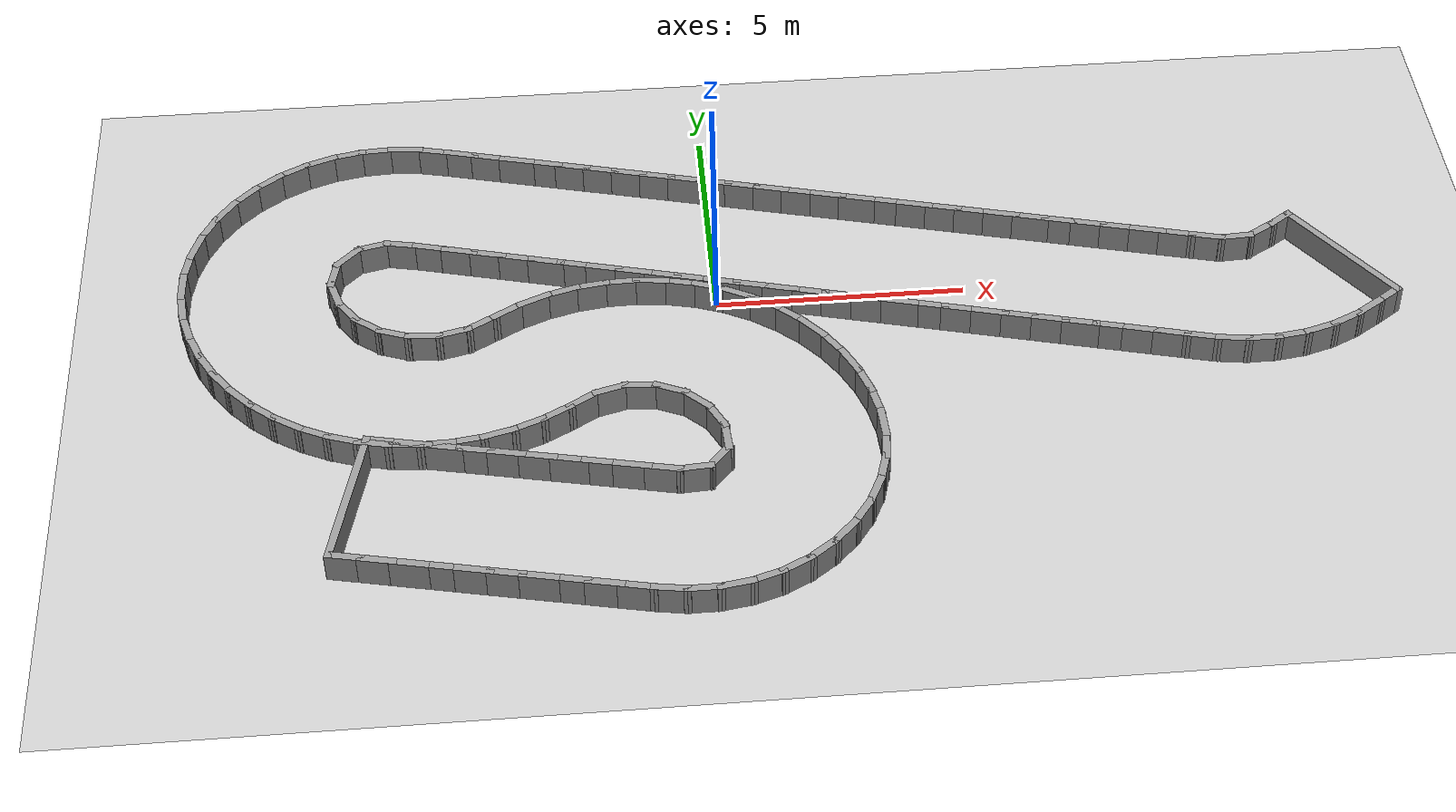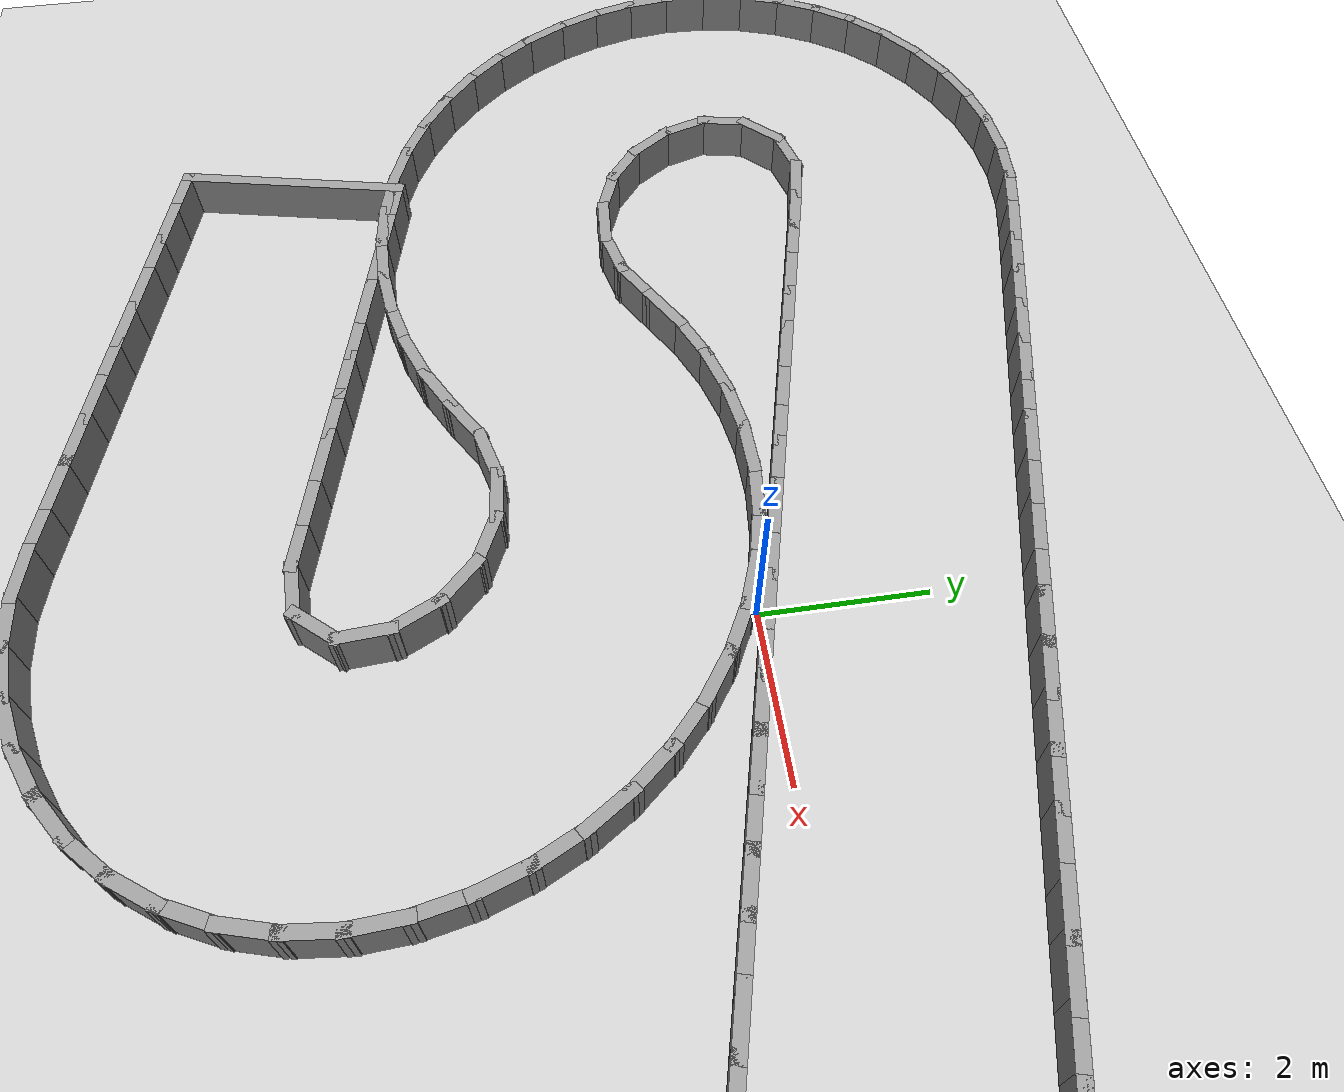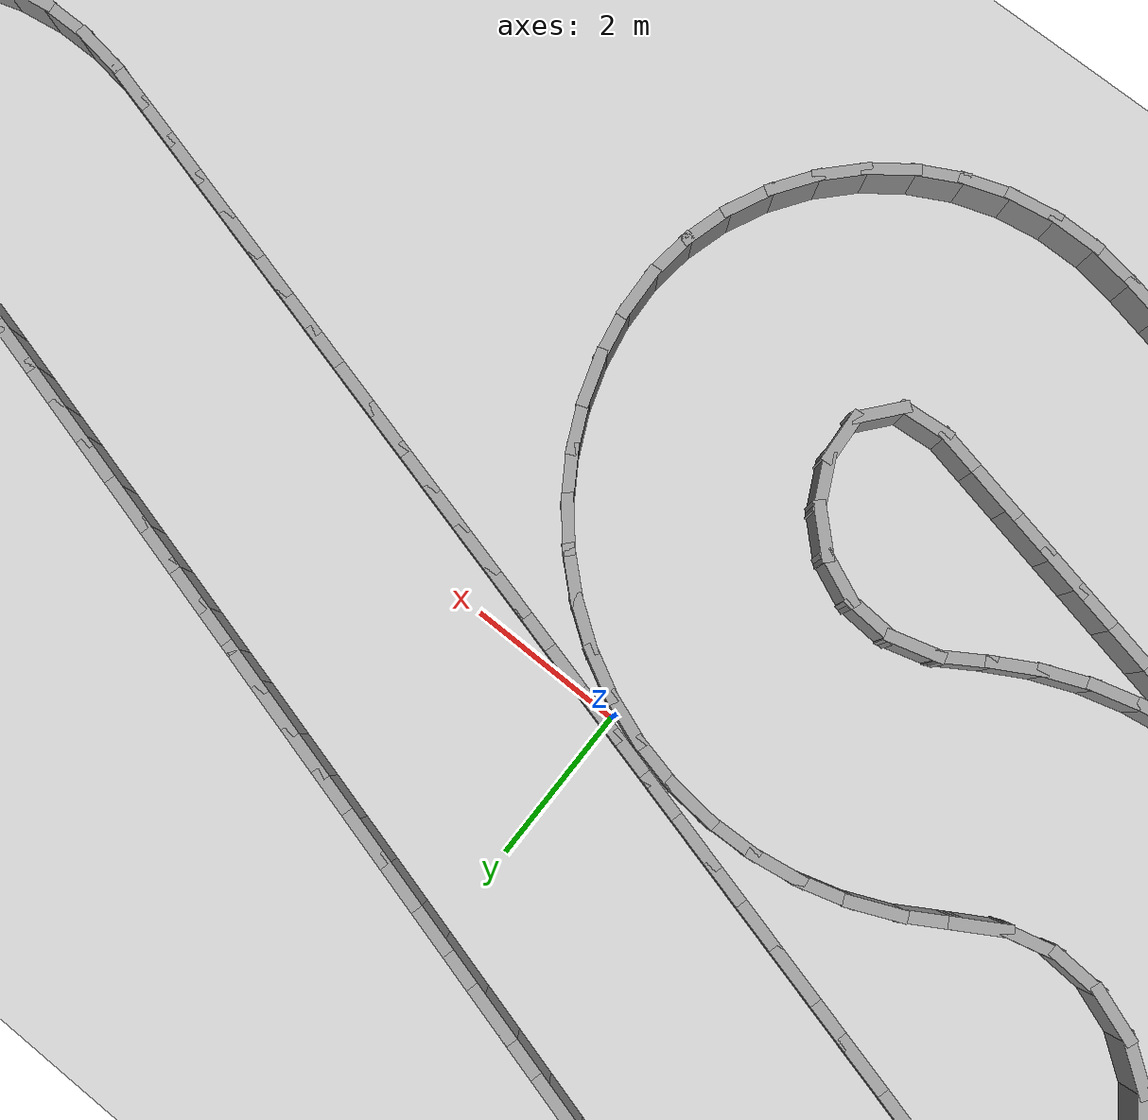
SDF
<?xml version="1.0" ?>
<sdf version='1.7'>
  <world name='default'>
    <plugin name='gazebo_ros_state' filename='libgazebo_ros_state.so'>
      <ros>
        <namespace>/</namespace>
      </ros>
      <update_rate>1000.0</update_rate>
    </plugin>

    <light name='sun' type='directional'>
      <cast_shadows>1</cast_shadows>
      <pose>0 0 10 0 -0 0</pose>
      <diffuse>0.8 0.8 0.8 1</diffuse>
      <specular>0.2 0.2 0.2 1</specular>
      <attenuation>
        <range>1000</range>
        <constant>0.9</constant>
        <linear>0.01</linear>
        <quadratic>0.001</quadratic>
      </attenuation>
      <direction>-0.5 0.1 -0.9</direction>
      <spot>
        <inner_angle>0</inner_angle>
        <outer_angle>0</outer_angle>
        <falloff>0</falloff>
      </spot>
    </light>
    <model name='ground_plane'>
      <static>1</static>
      <link name='link'>
        <collision name='collision'>
          <geometry>
            <plane>
              <normal>0 0 1</normal>
              <size>100 100</size>
            </plane>
          </geometry>
          <surface>
            <friction>
              <ode>
                <mu>100</mu>
                <mu2>50</mu2>
              </ode>
              <torsional>
                <ode/>
              </torsional>
            </friction>
            <contact>
              <ode/>
            </contact>
            <bounce/>
          </surface>
          <max_contacts>10</max_contacts>
        </collision>
        <visual name='visual'>
          <cast_shadows>0</cast_shadows>
          <geometry>
            <plane>
              <normal>0 0 1</normal>
              <size>100 100</size>
            </plane>
          </geometry>
          <material>
            <script>
              <uri>file://media/materials/scripts/gazebo.material</uri>
              <name>Gazebo/Grey</name>
            </script>
          </material>
        </visual>
        <self_collide>0</self_collide>
        <enable_wind>0</enable_wind>
        <kinematic>0</kinematic>
      </link>
    </model>
    <gravity>0 0 -9.8</gravity>
    <magnetic_field>6e-06 2.3e-05 -4.2e-05</magnetic_field>
    <atmosphere type='adiabatic'/>
    <physics type='ode'>
      <max_step_size>0.001</max_step_size>
      <real_time_factor>1</real_time_factor>
      <real_time_update_rate>1000</real_time_update_rate>
    </physics>
    <scene>
      <ambient>0.4 0.4 0.4 1</ambient>
      <background>0.7 0.7 0.7 1</background>
      <shadows>1</shadows>
    </scene>
    <audio>
      <device>default</device>
    </audio>
    <wind/>
    <spherical_coordinates>
      <surface_model>EARTH_WGS84</surface_model>
      <latitude_deg>0</latitude_deg>
      <longitude_deg>0</longitude_deg>
      <elevation>0</elevation>
      <heading_deg>0</heading_deg>
    </spherical_coordinates>
  <model name='rand_turn_01'>
    <pose>0 0 0 0 -0 0</pose>
    <link name='Wall_0'>
      <collision name='Wall_0_Collision'>
        <geometry><box><size>0.7500 0.1500 0.6000</size></box></geometry>
        <pose>0 0 0.3000 0 -0 0</pose>
      </collision>
      <visual name='Wall_0_Visual'>
        <pose>0 0 0.3000 0 -0 0</pose>
        <geometry><box><size>0.7500 0.1500 0.6000</size></box></geometry>
        <material>
          <script>
            <uri>file://media/materials/scripts/gazebo.material</uri>
            <name>Gazebo/Grey</name>
          </script>
          <ambient>1 1 1 1</ambient>
        </material>
      </visual>
      <pose>-6.5977 -3.8174 0 0 -0 -0.21750</pose>
    </link>
    <link name='Wall_1'>
      <collision name='Wall_1_Collision'>
        <geometry><box><size>0.7500 0.1500 0.6000</size></box></geometry>
        <pose>0 0 0.3000 0 -0 0</pose>
      </collision>
      <visual name='Wall_1_Visual'>
        <pose>0 0 0.3000 0 -0 0</pose>
        <geometry><box><size>0.7500 0.1500 0.6000</size></box></geometry>
        <material>
          <script>
            <uri>file://media/materials/scripts/gazebo.material</uri>
            <name>Gazebo/Grey</name>
          </script>
          <ambient>1 1 1 1</ambient>
        </material>
      </visual>
      <pose>-6.0118 -3.9469 0 0 -0 -0.21750</pose>
    </link>
    <link name='Wall_2'>
      <collision name='Wall_2_Collision'>
        <geometry><box><size>0.7500 0.1500 0.6000</size></box></geometry>
        <pose>0 0 0.3000 0 -0 0</pose>
      </collision>
      <visual name='Wall_2_Visual'>
        <pose>0 0 0.3000 0 -0 0</pose>
        <geometry><box><size>0.7500 0.1500 0.6000</size></box></geometry>
        <material>
          <script>
            <uri>file://media/materials/scripts/gazebo.material</uri>
            <name>Gazebo/Grey</name>
          </script>
          <ambient>1 1 1 1</ambient>
        </material>
      </visual>
      <pose>-5.4260 -4.0764 0 0 -0 -0.21750</pose>
    </link>
    <link name='Wall_3'>
      <collision name='Wall_3_Collision'>
        <geometry><box><size>0.7500 0.1500 0.6000</size></box></geometry>
        <pose>0 0 0.3000 0 -0 0</pose>
      </collision>
      <visual name='Wall_3_Visual'>
        <pose>0 0 0.3000 0 -0 0</pose>
        <geometry><box><size>0.7500 0.1500 0.6000</size></box></geometry>
        <material>
          <script>
            <uri>file://media/materials/scripts/gazebo.material</uri>
            <name>Gazebo/Grey</name>
          </script>
          <ambient>1 1 1 1</ambient>
        </material>
      </visual>
      <pose>-4.8401 -4.2058 0 0 -0 -0.21750</pose>
    </link>
    <link name='Wall_4'>
      <collision name='Wall_4_Collision'>
        <geometry><box><size>0.7500 0.1500 0.6000</size></box></geometry>
        <pose>0 0 0.3000 0 -0 0</pose>
      </collision>
      <visual name='Wall_4_Visual'>
        <pose>0 0 0.3000 0 -0 0</pose>
        <geometry><box><size>0.7500 0.1500 0.6000</size></box></geometry>
        <material>
          <script>
            <uri>file://media/materials/scripts/gazebo.material</uri>
            <name>Gazebo/Grey</name>
          </script>
          <ambient>1 1 1 1</ambient>
        </material>
      </visual>
      <pose>-4.2542 -4.3353 0 0 -0 -0.21750</pose>
    </link>
    <link name='Wall_5'>
      <collision name='Wall_5_Collision'>
        <geometry><box><size>0.7500 0.1500 0.6000</size></box></geometry>
        <pose>0 0 0.3000 0 -0 0</pose>
      </collision>
      <visual name='Wall_5_Visual'>
        <pose>0 0 0.3000 0 -0 0</pose>
        <geometry><box><size>0.7500 0.1500 0.6000</size></box></geometry>
        <material>
          <script>
            <uri>file://media/materials/scripts/gazebo.material</uri>
            <name>Gazebo/Grey</name>
          </script>
          <ambient>1 1 1 1</ambient>
        </material>
      </visual>
      <pose>-3.6684 -4.4648 0 0 -0 -0.21750</pose>
    </link>
    <link name='Wall_6'>
      <collision name='Wall_6_Collision'>
        <geometry><box><size>0.7500 0.1500 0.6000</size></box></geometry>
        <pose>0 0 0.3000 0 -0 0</pose>
      </collision>
      <visual name='Wall_6_Visual'>
        <pose>0 0 0.3000 0 -0 0</pose>
        <geometry><box><size>0.7500 0.1500 0.6000</size></box></geometry>
        <material>
          <script>
            <uri>file://media/materials/scripts/gazebo.material</uri>
            <name>Gazebo/Grey</name>
          </script>
          <ambient>1 1 1 1</ambient>
        </material>
      </visual>
      <pose>-3.0825 -4.5943 0 0 -0 -0.21750</pose>
    </link>
    <link name='Wall_7'>
      <collision name='Wall_7_Collision'>
        <geometry><box><size>0.7500 0.1500 0.6000</size></box></geometry>
        <pose>0 0 0.3000 0 -0 0</pose>
      </collision>
      <visual name='Wall_7_Visual'>
        <pose>0 0 0.3000 0 -0 0</pose>
        <geometry><box><size>0.7500 0.1500 0.6000</size></box></geometry>
        <material>
          <script>
            <uri>file://media/materials/scripts/gazebo.material</uri>
            <name>Gazebo/Grey</name>
          </script>
          <ambient>1 1 1 1</ambient>
        </material>
      </visual>
      <pose>-2.4967 -4.7237 0 0 -0 -0.21750</pose>
    </link>
    <link name='Wall_8'>
      <collision name='Wall_8_Collision'>
        <geometry><box><size>0.7500 0.1500 0.6000</size></box></geometry>
        <pose>0 0 0.3000 0 -0 0</pose>
      </collision>
      <visual name='Wall_8_Visual'>
        <pose>0 0 0.3000 0 -0 0</pose>
        <geometry><box><size>0.7500 0.1500 0.6000</size></box></geometry>
        <material>
          <script>
            <uri>file://media/materials/scripts/gazebo.material</uri>
            <name>Gazebo/Grey</name>
          </script>
          <ambient>1 1 1 1</ambient>
        </material>
      </visual>
      <pose>-1.9108 -4.8532 0 0 -0 -0.21750</pose>
    </link>
    <link name='Wall_9'>
      <collision name='Wall_9_Collision'>
        <geometry><box><size>0.7500 0.1500 0.6000</size></box></geometry>
        <pose>0 0 0.3000 0 -0 0</pose>
      </collision>
      <visual name='Wall_9_Visual'>
        <pose>0 0 0.3000 0 -0 0</pose>
        <geometry><box><size>0.7500 0.1500 0.6000</size></box></geometry>
        <material>
          <script>
            <uri>file://media/materials/scripts/gazebo.material</uri>
            <name>Gazebo/Grey</name>
          </script>
          <ambient>1 1 1 1</ambient>
        </material>
      </visual>
      <pose>-1.3249 -4.9827 0 0 -0 -0.21750</pose>
    </link>
    <link name='Wall_10'>
      <collision name='Wall_10_Collision'>
        <geometry><box><size>0.7354 0.1500 0.6000</size></box></geometry>
        <pose>0 0 0.3000 0 -0 0</pose>
      </collision>
      <visual name='Wall_10_Visual'>
        <pose>0 0 0.3000 0 -0 0</pose>
        <geometry><box><size>0.7354 0.1500 0.6000</size></box></geometry>
        <material>
          <script>
            <uri>file://media/materials/scripts/gazebo.material</uri>
            <name>Gazebo/Grey</name>
          </script>
          <ambient>1 1 1 1</ambient>
        </material>
      </visual>
      <pose>-0.7400 -5.0276 0 0 -0 0.06791</pose>
    </link>
    <link name='Wall_11'>
      <collision name='Wall_11_Collision'>
        <geometry><box><size>0.7332 0.1500 0.6000</size></box></geometry>
        <pose>0 0 0.3000 0 -0 0</pose>
      </collision>
      <visual name='Wall_11_Visual'>
        <pose>0 0 0.3000 0 -0 0</pose>
        <geometry><box><size>0.7332 0.1500 0.6000</size></box></geometry>
        <material>
          <script>
            <uri>file://media/materials/scripts/gazebo.material</uri>
            <name>Gazebo/Grey</name>
          </script>
          <ambient>1 1 1 1</ambient>
        </material>
      </visual>
      <pose>-0.2620 -4.7831 0 0 -0 0.87923</pose>
    </link>
    <link name='Wall_12'>
      <collision name='Wall_12_Collision'>
        <geometry><box><size>0.7419 0.1500 0.6000</size></box></geometry>
        <pose>0 0 0.3000 0 -0 0</pose>
      </collision>
      <visual name='Wall_12_Visual'>
        <pose>0 0 0.3000 0 -0 0</pose>
        <geometry><box><size>0.7419 0.1500 0.6000</size></box></geometry>
        <material>
          <script>
            <uri>file://media/materials/scripts/gazebo.material</uri>
            <name>Gazebo/Grey</name>
          </script>
          <ambient>1 1 1 1</ambient>
        </material>
      </visual>
      <pose>-0.0944 -4.2631 0 0 -0 1.63312</pose>
    </link>
    <link name='Wall_13'>
      <collision name='Wall_13_Collision'>
        <geometry><box><size>0.7470 0.1500 0.6000</size></box></geometry>
        <pose>0 0 0.3000 0 -0 0</pose>
      </collision>
      <visual name='Wall_13_Visual'>
        <pose>0 0 0.3000 0 -0 0</pose>
        <geometry><box><size>0.7470 0.1500 0.6000</size></box></geometry>
        <material>
          <script>
            <uri>file://media/materials/scripts/gazebo.material</uri>
            <name>Gazebo/Grey</name>
          </script>
          <ambient>1 1 1 1</ambient>
        </material>
      </visual>
      <pose>-0.2440 -3.6996 0 0 -0 2.02571</pose>
    </link>
    <link name='Wall_14'>
      <collision name='Wall_14_Collision'>
        <geometry><box><size>0.7470 0.1500 0.6000</size></box></geometry>
        <pose>0 0 0.3000 0 -0 0</pose>
      </collision>
      <visual name='Wall_14_Visual'>
        <pose>0 0 0.3000 0 -0 0</pose>
        <geometry><box><size>0.7470 0.1500 0.6000</size></box></geometry>
        <material>
          <script>
            <uri>file://media/materials/scripts/gazebo.material</uri>
            <name>Gazebo/Grey</name>
          </script>
          <ambient>1 1 1 1</ambient>
        </material>
      </visual>
      <pose>-0.5888 -3.2229 0 0 -0 2.36825</pose>
    </link>
    <link name='Wall_15'>
      <collision name='Wall_15_Collision'>
        <geometry><box><size>0.7466 0.1500 0.6000</size></box></geometry>
        <pose>0 0 0.3000 0 -0 0</pose>
      </collision>
      <visual name='Wall_15_Visual'>
        <pose>0 0 0.3000 0 -0 0</pose>
        <geometry><box><size>0.7466 0.1500 0.6000</size></box></geometry>
        <material>
          <script>
            <uri>file://media/materials/scripts/gazebo.material</uri>
            <name>Gazebo/Grey</name>
          </script>
          <ambient>1 1 1 1</ambient>
        </material>
      </visual>
      <pose>-1.0746 -2.8924 0 0 -0 2.72031</pose>
    </link>
    <link name='Wall_16'>
      <collision name='Wall_16_Collision'>
        <geometry><box><size>0.7470 0.1500 0.6000</size></box></geometry>
        <pose>0 0 0.3000 0 -0 0</pose>
      </collision>
      <visual name='Wall_16_Visual'>
        <pose>0 0 0.3000 0 -0 0</pose>
        <geometry><box><size>0.7470 0.1500 0.6000</size></box></geometry>
        <material>
          <script>
            <uri>file://media/materials/scripts/gazebo.material</uri>
            <name>Gazebo/Grey</name>
          </script>
          <ambient>1 1 1 1</ambient>
        </material>
      </visual>
      <pose>-1.6446 -2.7495 0 0 -0 3.07132</pose>
    </link>
    <link name='Wall_17'>
      <collision name='Wall_17_Collision'>
        <geometry><box><size>0.7470 0.1500 0.6000</size></box></geometry>
        <pose>0 0 0.3000 0 -0 0</pose>
      </collision>
      <visual name='Wall_17_Visual'>
        <pose>0 0 0.3000 0 -0 0</pose>
        <geometry><box><size>0.7470 0.1500 0.6000</size></box></geometry>
        <material>
          <script>
            <uri>file://media/materials/scripts/gazebo.material</uri>
            <name>Gazebo/Grey</name>
          </script>
          <ambient>1 1 1 1</ambient>
        </material>
      </visual>
      <pose>-2.2299 -2.8090 0 0 -0 -2.86868</pose>
    </link>
    <link name='Wall_18'>
      <collision name='Wall_18_Collision'>
        <geometry><box><size>0.7492 0.1500 0.6000</size></box></geometry>
        <pose>0 0 0.3000 0 -0 0</pose>
      </collision>
      <visual name='Wall_18_Visual'>
        <pose>0 0 0.3000 0 -0 0</pose>
        <geometry><box><size>0.7492 0.1500 0.6000</size></box></geometry>
        <material>
          <script>
            <uri>file://media/materials/scripts/gazebo.material</uri>
            <name>Gazebo/Grey</name>
          </script>
          <ambient>1 1 1 1</ambient>
        </material>
      </visual>
      <pose>-2.7704 -3.0499 0 0 -0 -2.57645</pose>
    </link>
    <link name='Wall_19'>
      <collision name='Wall_19_Collision'>
        <geometry><box><size>0.7496 0.1500 0.6000</size></box></geometry>
        <pose>0 0 0.3000 0 -0 0</pose>
      </collision>
      <visual name='Wall_19_Visual'>
        <pose>0 0 0.3000 0 -0 0</pose>
        <geometry><box><size>0.7496 0.1500 0.6000</size></box></geometry>
        <material>
          <script>
            <uri>file://media/materials/scripts/gazebo.material</uri>
            <name>Gazebo/Grey</name>
          </script>
          <ambient>1 1 1 1</ambient>
        </material>
      </visual>
      <pose>-3.2849 -3.3568 0 0 -0 -2.63097</pose>
    </link>
    <link name='Wall_20'>
      <collision name='Wall_20_Collision'>
        <geometry><box><size>0.7496 0.1500 0.6000</size></box></geometry>
        <pose>0 0 0.3000 0 -0 0</pose>
      </collision>
      <visual name='Wall_20_Visual'>
        <pose>0 0 0.3000 0 -0 0</pose>
        <geometry><box><size>0.7496 0.1500 0.6000</size></box></geometry>
        <material>
          <script>
            <uri>file://media/materials/scripts/gazebo.material</uri>
            <name>Gazebo/Grey</name>
          </script>
          <ambient>1 1 1 1</ambient>
        </material>
      </visual>
      <pose>-3.8238 -3.6173 0 0 -0 -2.75171</pose>
    </link>
    <link name='Wall_21'>
      <collision name='Wall_21_Collision'>
        <geometry><box><size>0.7496 0.1500 0.6000</size></box></geometry>
        <pose>0 0 0.3000 0 -0 0</pose>
      </collision>
      <visual name='Wall_21_Visual'>
        <pose>0 0 0.3000 0 -0 0</pose>
        <geometry><box><size>0.7496 0.1500 0.6000</size></box></geometry>
        <material>
          <script>
            <uri>file://media/materials/scripts/gazebo.material</uri>
            <name>Gazebo/Grey</name>
          </script>
          <ambient>1 1 1 1</ambient>
        </material>
      </visual>
      <pose>-4.3901 -3.8110 0 0 -0 -2.87246</pose>
    </link>
    <link name='Wall_22'>
      <collision name='Wall_22_Collision'>
        <geometry><box><size>0.7496 0.1500 0.6000</size></box></geometry>
        <pose>0 0 0.3000 0 -0 0</pose>
      </collision>
      <visual name='Wall_22_Visual'>
        <pose>0 0 0.3000 0 -0 0</pose>
        <geometry><box><size>0.7496 0.1500 0.6000</size></box></geometry>
        <material>
          <script>
            <uri>file://media/materials/scripts/gazebo.material</uri>
            <name>Gazebo/Grey</name>
          </script>
          <ambient>1 1 1 1</ambient>
        </material>
      </visual>
      <pose>-4.9757 -3.9349 0 0 -0 -2.99349</pose>
    </link>
    <link name='Wall_23'>
      <collision name='Wall_23_Collision'>
        <geometry><box><size>0.7496 0.1500 0.6000</size></box></geometry>
        <pose>0 0 0.3000 0 -0 0</pose>
      </collision>
      <visual name='Wall_23_Visual'>
        <pose>0 0 0.3000 0 -0 0</pose>
        <geometry><box><size>0.7496 0.1500 0.6000</size></box></geometry>
        <material>
          <script>
            <uri>file://media/materials/scripts/gazebo.material</uri>
            <name>Gazebo/Grey</name>
          </script>
          <ambient>1 1 1 1</ambient>
        </material>
      </visual>
      <pose>-5.5719 -3.9870 0 0 -0 -3.11536</pose>
    </link>
    <link name='Wall_24'>
      <collision name='Wall_24_Collision'>
        <geometry><box><size>0.7496 0.1500 0.6000</size></box></geometry>
        <pose>0 0 0.3000 0 -0 0</pose>
      </collision>
      <visual name='Wall_24_Visual'>
        <pose>0 0 0.3000 0 -0 0</pose>
        <geometry><box><size>0.7496 0.1500 0.6000</size></box></geometry>
        <material>
          <script>
            <uri>file://media/materials/scripts/gazebo.material</uri>
            <name>Gazebo/Grey</name>
          </script>
          <ambient>1 1 1 1</ambient>
        </material>
      </visual>
      <pose>-6.1701 -3.9666 0 0 -0 3.04708</pose>
    </link>
    <link name='Wall_25'>
      <collision name='Wall_25_Collision'>
        <geometry><box><size>0.7496 0.1500 0.6000</size></box></geometry>
        <pose>0 0 0.3000 0 -0 0</pose>
      </collision>
      <visual name='Wall_25_Visual'>
        <pose>0 0 0.3000 0 -0 0</pose>
        <geometry><box><size>0.7496 0.1500 0.6000</size></box></geometry>
        <material>
          <script>
            <uri>file://media/materials/scripts/gazebo.material</uri>
            <name>Gazebo/Grey</name>
          </script>
          <ambient>1 1 1 1</ambient>
        </material>
      </visual>
      <pose>-6.7614 -3.8743 0 0 -0 2.92633</pose>
    </link>
    <link name='Wall_26'>
      <collision name='Wall_26_Collision'>
        <geometry><box><size>0.7496 0.1500 0.6000</size></box></geometry>
        <pose>0 0 0.3000 0 -0 0</pose>
      </collision>
      <visual name='Wall_26_Visual'>
        <pose>0 0 0.3000 0 -0 0</pose>
        <geometry><box><size>0.7496 0.1500 0.6000</size></box></geometry>
        <material>
          <script>
            <uri>file://media/materials/scripts/gazebo.material</uri>
            <name>Gazebo/Grey</name>
          </script>
          <ambient>1 1 1 1</ambient>
        </material>
      </visual>
      <pose>-7.3373 -3.7114 0 0 -0 2.80559</pose>
    </link>
    <link name='Wall_27'>
      <collision name='Wall_27_Collision'>
        <geometry><box><size>0.7496 0.1500 0.6000</size></box></geometry>
        <pose>0 0 0.3000 0 -0 0</pose>
      </collision>
      <visual name='Wall_27_Visual'>
        <pose>0 0 0.3000 0 -0 0</pose>
        <geometry><box><size>0.7496 0.1500 0.6000</size></box></geometry>
        <material>
          <script>
            <uri>file://media/materials/scripts/gazebo.material</uri>
            <name>Gazebo/Grey</name>
          </script>
          <ambient>1 1 1 1</ambient>
        </material>
      </visual>
      <pose>-7.8894 -3.4801 0 0 -0 2.68430</pose>
    </link>
    <link name='Wall_28'>
      <collision name='Wall_28_Collision'>
        <geometry><box><size>0.7496 0.1500 0.6000</size></box></geometry>
        <pose>0 0 0.3000 0 -0 0</pose>
      </collision>
      <visual name='Wall_28_Visual'>
        <pose>0 0 0.3000 0 -0 0</pose>
        <geometry><box><size>0.7496 0.1500 0.6000</size></box></geometry>
        <material>
          <script>
            <uri>file://media/materials/scripts/gazebo.material</uri>
            <name>Gazebo/Grey</name>
          </script>
          <ambient>1 1 1 1</ambient>
        </material>
      </visual>
      <pose>-8.4094 -3.1837 0 0 -0 2.56268</pose>
    </link>
    <link name='Wall_29'>
      <collision name='Wall_29_Collision'>
        <geometry><box><size>0.7496 0.1500 0.6000</size></box></geometry>
        <pose>0 0 0.3000 0 -0 0</pose>
      </collision>
      <visual name='Wall_29_Visual'>
        <pose>0 0 0.3000 0 -0 0</pose>
        <geometry><box><size>0.7496 0.1500 0.6000</size></box></geometry>
        <material>
          <script>
            <uri>file://media/materials/scripts/gazebo.material</uri>
            <name>Gazebo/Grey</name>
          </script>
          <ambient>1 1 1 1</ambient>
        </material>
      </visual>
      <pose>-8.8897 -2.8267 0 0 -0 2.44194</pose>
    </link>
    <link name='Wall_30'>
      <collision name='Wall_30_Collision'>
        <geometry><box><size>0.7496 0.1500 0.6000</size></box></geometry>
        <pose>0 0 0.3000 0 -0 0</pose>
      </collision>
      <visual name='Wall_30_Visual'>
        <pose>0 0 0.3000 0 -0 0</pose>
        <geometry><box><size>0.7496 0.1500 0.6000</size></box></geometry>
        <material>
          <script>
            <uri>file://media/materials/scripts/gazebo.material</uri>
            <name>Gazebo/Grey</name>
          </script>
          <ambient>1 1 1 1</ambient>
        </material>
      </visual>
      <pose>-9.3235 -2.4143 0 0 -0 2.32119</pose>
    </link>
    <link name='Wall_31'>
      <collision name='Wall_31_Collision'>
        <geometry><box><size>0.7496 0.1500 0.6000</size></box></geometry>
        <pose>0 0 0.3000 0 -0 0</pose>
      </collision>
      <visual name='Wall_31_Visual'>
        <pose>0 0 0.3000 0 -0 0</pose>
        <geometry><box><size>0.7496 0.1500 0.6000</size></box></geometry>
        <material>
          <script>
            <uri>file://media/materials/scripts/gazebo.material</uri>
            <name>Gazebo/Grey</name>
          </script>
          <ambient>1 1 1 1</ambient>
        </material>
      </visual>
      <pose>-9.7045 -1.9527 0 0 -0 2.20045</pose>
    </link>
    <link name='Wall_32'>
      <collision name='Wall_32_Collision'>
        <geometry><box><size>0.7496 0.1500 0.6000</size></box></geometry>
        <pose>0 0 0.3000 0 -0 0</pose>
      </collision>
      <visual name='Wall_32_Visual'>
        <pose>0 0 0.3000 0 -0 0</pose>
        <geometry><box><size>0.7496 0.1500 0.6000</size></box></geometry>
        <material>
          <script>
            <uri>file://media/materials/scripts/gazebo.material</uri>
            <name>Gazebo/Grey</name>
          </script>
          <ambient>1 1 1 1</ambient>
        </material>
      </visual>
      <pose>-10.0269 -1.4485 0 0 -0 2.07890</pose>
    </link>
    <link name='Wall_33'>
      <collision name='Wall_33_Collision'>
        <geometry><box><size>0.7496 0.1500 0.6000</size></box></geometry>
        <pose>0 0 0.3000 0 -0 0</pose>
      </collision>
      <visual name='Wall_33_Visual'>
        <pose>0 0 0.3000 0 -0 0</pose>
        <geometry><box><size>0.7496 0.1500 0.6000</size></box></geometry>
        <material>
          <script>
            <uri>file://media/materials/scripts/gazebo.material</uri>
            <name>Gazebo/Grey</name>
          </script>
          <ambient>1 1 1 1</ambient>
        </material>
      </visual>
      <pose>-10.2858 -0.9089 0 0 -0 1.95754</pose>
    </link>
    <link name='Wall_34'>
      <collision name='Wall_34_Collision'>
        <geometry><box><size>0.7495 0.1500 0.6000</size></box></geometry>
        <pose>0 0 0.3000 0 -0 0</pose>
      </collision>
      <visual name='Wall_34_Visual'>
        <pose>0 0 0.3000 0 -0 0</pose>
        <geometry><box><size>0.7495 0.1500 0.6000</size></box></geometry>
        <material>
          <script>
            <uri>file://media/materials/scripts/gazebo.material</uri>
            <name>Gazebo/Grey</name>
          </script>
          <ambient>1 1 1 1</ambient>
        </material>
      </visual>
      <pose>-10.4773 -0.3419 0 0 -0 1.83542</pose>
    </link>
    <link name='Wall_35'>
      <collision name='Wall_35_Collision'>
        <geometry><box><size>0.7494 0.1500 0.6000</size></box></geometry>
        <pose>0 0 0.3000 0 -0 0</pose>
      </collision>
      <visual name='Wall_35_Visual'>
        <pose>0 0 0.3000 0 -0 0</pose>
        <geometry><box><size>0.7494 0.1500 0.6000</size></box></geometry>
        <material>
          <script>
            <uri>file://media/materials/scripts/gazebo.material</uri>
            <name>Gazebo/Grey</name>
          </script>
          <ambient>1 1 1 1</ambient>
        </material>
      </visual>
      <pose>-10.5922 0.2449 0 0 -0 1.69281</pose>
    </link>
    <link name='Wall_36'>
      <collision name='Wall_36_Collision'>
        <geometry><box><size>0.7495 0.1500 0.6000</size></box></geometry>
        <pose>0 0 0.3000 0 -0 0</pose>
      </collision>
      <visual name='Wall_36_Visual'>
        <pose>0 0 0.3000 0 -0 0</pose>
        <geometry><box><size>0.7495 0.1500 0.6000</size></box></geometry>
        <material>
          <script>
            <uri>file://media/materials/scripts/gazebo.material</uri>
            <name>Gazebo/Grey</name>
          </script>
          <ambient>1 1 1 1</ambient>
        </material>
      </visual>
      <pose>-10.6208 0.8420 0 0 -0 1.54438</pose>
    </link>
    <link name='Wall_37'>
      <collision name='Wall_37_Collision'>
        <geometry><box><size>0.7494 0.1500 0.6000</size></box></geometry>
        <pose>0 0 0.3000 0 -0 0</pose>
      </collision>
      <visual name='Wall_37_Visual'>
        <pose>0 0 0.3000 0 -0 0</pose>
        <geometry><box><size>0.7494 0.1500 0.6000</size></box></geometry>
        <material>
          <script>
            <uri>file://media/materials/scripts/gazebo.material</uri>
            <name>Gazebo/Grey</name>
          </script>
          <ambient>1 1 1 1</ambient>
        </material>
      </visual>
      <pose>-10.5602 1.4367 0 0 -0 1.39420</pose>
    </link>
    <link name='Wall_38'>
      <collision name='Wall_38_Collision'>
        <geometry><box><size>0.7494 0.1500 0.6000</size></box></geometry>
        <pose>0 0 0.3000 0 -0 0</pose>
      </collision>
      <visual name='Wall_38_Visual'>
        <pose>0 0 0.3000 0 -0 0</pose>
        <geometry><box><size>0.7494 0.1500 0.6000</size></box></geometry>
        <material>
          <script>
            <uri>file://media/materials/scripts/gazebo.material</uri>
            <name>Gazebo/Grey</name>
          </script>
          <ambient>1 1 1 1</ambient>
        </material>
      </visual>
      <pose>-10.4119 2.0158 0 0 -0 1.24597</pose>
    </link>
    <link name='Wall_39'>
      <collision name='Wall_39_Collision'>
        <geometry><box><size>0.7494 0.1500 0.6000</size></box></geometry>
        <pose>0 0 0.3000 0 -0 0</pose>
      </collision>
      <visual name='Wall_39_Visual'>
        <pose>0 0 0.3000 0 -0 0</pose>
        <geometry><box><size>0.7494 0.1500 0.6000</size></box></geometry>
        <material>
          <script>
            <uri>file://media/materials/scripts/gazebo.material</uri>
            <name>Gazebo/Grey</name>
          </script>
          <ambient>1 1 1 1</ambient>
        </material>
      </visual>
      <pose>-10.1797 2.5666 0 0 -0 1.09773</pose>
    </link>
    <link name='Wall_40'>
      <collision name='Wall_40_Collision'>
        <geometry><box><size>0.7494 0.1500 0.6000</size></box></geometry>
        <pose>0 0 0.3000 0 -0 0</pose>
      </collision>
      <visual name='Wall_40_Visual'>
        <pose>0 0 0.3000 0 -0 0</pose>
        <geometry><box><size>0.7494 0.1500 0.6000</size></box></geometry>
        <material>
          <script>
            <uri>file://media/materials/scripts/gazebo.material</uri>
            <name>Gazebo/Grey</name>
          </script>
          <ambient>1 1 1 1</ambient>
        </material>
      </visual>
      <pose>-9.8687 3.0770 0 0 -0 0.94943</pose>
    </link>
    <link name='Wall_41'>
      <collision name='Wall_41_Collision'>
        <geometry><box><size>0.7494 0.1500 0.6000</size></box></geometry>
        <pose>0 0 0.3000 0 -0 0</pose>
      </collision>
      <visual name='Wall_41_Visual'>
        <pose>0 0 0.3000 0 -0 0</pose>
        <geometry><box><size>0.7494 0.1500 0.6000</size></box></geometry>
        <material>
          <script>
            <uri>file://media/materials/scripts/gazebo.material</uri>
            <name>Gazebo/Grey</name>
          </script>
          <ambient>1 1 1 1</ambient>
        </material>
      </visual>
      <pose>-9.4841 3.5344 0 0 -0 0.79378</pose>
    </link>
    <link name='Wall_42'>
      <collision name='Wall_42_Collision'>
        <geometry><box><size>0.7494 0.1500 0.6000</size></box></geometry>
        <pose>0 0 0.3000 0 -0 0</pose>
      </collision>
      <visual name='Wall_42_Visual'>
        <pose>0 0 0.3000 0 -0 0</pose>
        <geometry><box><size>0.7494 0.1500 0.6000</size></box></geometry>
        <material>
          <script>
            <uri>file://media/materials/scripts/gazebo.material</uri>
            <name>Gazebo/Grey</name>
          </script>
          <ambient>1 1 1 1</ambient>
        </material>
      </visual>
      <pose>-9.0342 3.9279 0 0 -0 0.64353</pose>
    </link>
    <link name='Wall_43'>
      <collision name='Wall_43_Collision'>
        <geometry><box><size>0.7494 0.1500 0.6000</size></box></geometry>
        <pose>0 0 0.3000 0 -0 0</pose>
      </collision>
      <visual name='Wall_43_Visual'>
        <pose>0 0 0.3000 0 -0 0</pose>
        <geometry><box><size>0.7494 0.1500 0.6000</size></box></geometry>
        <material>
          <script>
            <uri>file://media/materials/scripts/gazebo.material</uri>
            <name>Gazebo/Grey</name>
          </script>
          <ambient>1 1 1 1</ambient>
        </material>
      </visual>
      <pose>-8.5309 4.2505 0 0 -0 0.49657</pose>
    </link>
    <link name='Wall_44'>
      <collision name='Wall_44_Collision'>
        <geometry><box><size>0.7494 0.1500 0.6000</size></box></geometry>
        <pose>0 0 0.3000 0 -0 0</pose>
      </collision>
      <visual name='Wall_44_Visual'>
        <pose>0 0 0.3000 0 -0 0</pose>
        <geometry><box><size>0.7494 0.1500 0.6000</size></box></geometry>
        <material>
          <script>
            <uri>file://media/materials/scripts/gazebo.material</uri>
            <name>Gazebo/Grey</name>
          </script>
          <ambient>1 1 1 1</ambient>
        </material>
      </visual>
      <pose>-7.9859 4.4959 0 0 -0 0.34960</pose>
    </link>
    <link name='Wall_45'>
      <collision name='Wall_45_Collision'>
        <geometry><box><size>0.7494 0.1500 0.6000</size></box></geometry>
        <pose>0 0 0.3000 0 -0 0</pose>
      </collision>
      <visual name='Wall_45_Visual'>
        <pose>0 0 0.3000 0 -0 0</pose>
        <geometry><box><size>0.7494 0.1500 0.6000</size></box></geometry>
        <material>
          <script>
            <uri>file://media/materials/scripts/gazebo.material</uri>
            <name>Gazebo/Grey</name>
          </script>
          <ambient>1 1 1 1</ambient>
        </material>
      </visual>
      <pose>-7.4107 4.6589 0 0 -0 0.20264</pose>
    </link>
    <link name='Wall_46'>
      <collision name='Wall_46_Collision'>
        <geometry><box><size>0.7495 0.1500 0.6000</size></box></geometry>
        <pose>0 0 0.3000 0 -0 0</pose>
      </collision>
      <visual name='Wall_46_Visual'>
        <pose>0 0 0.3000 0 -0 0</pose>
        <geometry><box><size>0.7495 0.1500 0.6000</size></box></geometry>
        <material>
          <script>
            <uri>file://media/materials/scripts/gazebo.material</uri>
            <name>Gazebo/Grey</name>
          </script>
          <ambient>1 1 1 1</ambient>
        </material>
      </visual>
      <pose>-6.8179 4.7358 0 0 -0 0.05521</pose>
    </link>
    <link name='Wall_47'>
      <collision name='Wall_47_Collision'>
        <geometry><box><size>0.7494 0.1500 0.6000</size></box></geometry>
        <pose>0 0 0.3000 0 -0 0</pose>
      </collision>
      <visual name='Wall_47_Visual'>
        <pose>0 0 0.3000 0 -0 0</pose>
        <geometry><box><size>0.7494 0.1500 0.6000</size></box></geometry>
        <material>
          <script>
            <uri>file://media/materials/scripts/gazebo.material</uri>
            <name>Gazebo/Grey</name>
          </script>
          <ambient>1 1 1 1</ambient>
        </material>
      </visual>
      <pose>-6.2202 4.7244 0 0 -0 -0.09311</pose>
    </link>
    <link name='Wall_48'>
      <collision name='Wall_48_Collision'>
        <geometry><box><size>0.7497 0.1500 0.6000</size></box></geometry>
        <pose>0 0 0.3000 0 -0 0</pose>
      </collision>
      <visual name='Wall_48_Visual'>
        <pose>0 0 0.3000 0 -0 0</pose>
        <geometry><box><size>0.7497 0.1500 0.6000</size></box></geometry>
        <material>
          <script>
            <uri>file://media/materials/scripts/gazebo.material</uri>
            <name>Gazebo/Grey</name>
          </script>
          <ambient>1 1 1 1</ambient>
        </material>
      </visual>
      <pose>-5.6296 4.6290 0 0 -0 -0.22733</pose>
    </link>
    <link name='Wall_49'>
      <collision name='Wall_49_Collision'>
        <geometry><box><size>0.7500 0.1500 0.6000</size></box></geometry>
        <pose>0 0 0.3000 0 -0 0</pose>
      </collision>
      <visual name='Wall_49_Visual'>
        <pose>0 0 0.3000 0 -0 0</pose>
        <geometry><box><size>0.7500 0.1500 0.6000</size></box></geometry>
        <material>
          <script>
            <uri>file://media/materials/scripts/gazebo.material</uri>
            <name>Gazebo/Grey</name>
          </script>
          <ambient>1 1 1 1</ambient>
        </material>
      </visual>
      <pose>-5.0472 4.4857 0 0 -0 -0.25506</pose>
    </link>
    <link name='Wall_50'>
      <collision name='Wall_50_Collision'>
        <geometry><box><size>0.7500 0.1500 0.6000</size></box></geometry>
        <pose>0 0 0.3000 0 -0 0</pose>
      </collision>
      <visual name='Wall_50_Visual'>
        <pose>0 0 0.3000 0 -0 0</pose>
        <geometry><box><size>0.7500 0.1500 0.6000</size></box></geometry>
        <material>
          <script>
            <uri>file://media/materials/scripts/gazebo.material</uri>
            <name>Gazebo/Grey</name>
          </script>
          <ambient>1 1 1 1</ambient>
        </material>
      </visual>
      <pose>-4.4666 4.3343 0 0 -0 -0.25506</pose>
    </link>
    <link name='Wall_51'>
      <collision name='Wall_51_Collision'>
        <geometry><box><size>0.7500 0.1500 0.6000</size></box></geometry>
        <pose>0 0 0.3000 0 -0 0</pose>
      </collision>
      <visual name='Wall_51_Visual'>
        <pose>0 0 0.3000 0 -0 0</pose>
        <geometry><box><size>0.7500 0.1500 0.6000</size></box></geometry>
        <material>
          <script>
            <uri>file://media/materials/scripts/gazebo.material</uri>
            <name>Gazebo/Grey</name>
          </script>
          <ambient>1 1 1 1</ambient>
        </material>
      </visual>
      <pose>-3.8860 4.1829 0 0 -0 -0.25506</pose>
    </link>
    <link name='Wall_52'>
      <collision name='Wall_52_Collision'>
        <geometry><box><size>0.7500 0.1500 0.6000</size></box></geometry>
        <pose>0 0 0.3000 0 -0 0</pose>
      </collision>
      <visual name='Wall_52_Visual'>
        <pose>0 0 0.3000 0 -0 0</pose>
        <geometry><box><size>0.7500 0.1500 0.6000</size></box></geometry>
        <material>
          <script>
            <uri>file://media/materials/scripts/gazebo.material</uri>
            <name>Gazebo/Grey</name>
          </script>
          <ambient>1 1 1 1</ambient>
        </material>
      </visual>
      <pose>-3.3054 4.0316 0 0 -0 -0.25506</pose>
    </link>
    <link name='Wall_53'>
      <collision name='Wall_53_Collision'>
        <geometry><box><size>0.7500 0.1500 0.6000</size></box></geometry>
        <pose>0 0 0.3000 0 -0 0</pose>
      </collision>
      <visual name='Wall_53_Visual'>
        <pose>0 0 0.3000 0 -0 0</pose>
        <geometry><box><size>0.7500 0.1500 0.6000</size></box></geometry>
        <material>
          <script>
            <uri>file://media/materials/scripts/gazebo.material</uri>
            <name>Gazebo/Grey</name>
          </script>
          <ambient>1 1 1 1</ambient>
        </material>
      </visual>
      <pose>-2.7248 3.8802 0 0 -0 -0.25506</pose>
    </link>
    <link name='Wall_54'>
      <collision name='Wall_54_Collision'>
        <geometry><box><size>0.7500 0.1500 0.6000</size></box></geometry>
        <pose>0 0 0.3000 0 -0 0</pose>
      </collision>
      <visual name='Wall_54_Visual'>
        <pose>0 0 0.3000 0 -0 0</pose>
        <geometry><box><size>0.7500 0.1500 0.6000</size></box></geometry>
        <material>
          <script>
            <uri>file://media/materials/scripts/gazebo.material</uri>
            <name>Gazebo/Grey</name>
          </script>
          <ambient>1 1 1 1</ambient>
        </material>
      </visual>
      <pose>-2.1442 3.7288 0 0 -0 -0.25506</pose>
    </link>
    <link name='Wall_55'>
      <collision name='Wall_55_Collision'>
        <geometry><box><size>0.7500 0.1500 0.6000</size></box></geometry>
        <pose>0 0 0.3000 0 -0 0</pose>
      </collision>
      <visual name='Wall_55_Visual'>
        <pose>0 0 0.3000 0 -0 0</pose>
        <geometry><box><size>0.7500 0.1500 0.6000</size></box></geometry>
        <material>
          <script>
            <uri>file://media/materials/scripts/gazebo.material</uri>
            <name>Gazebo/Grey</name>
          </script>
          <ambient>1 1 1 1</ambient>
        </material>
      </visual>
      <pose>-1.5636 3.5774 0 0 -0 -0.25506</pose>
    </link>
    <link name='Wall_56'>
      <collision name='Wall_56_Collision'>
        <geometry><box><size>0.7500 0.1500 0.6000</size></box></geometry>
        <pose>0 0 0.3000 0 -0 0</pose>
      </collision>
      <visual name='Wall_56_Visual'>
        <pose>0 0 0.3000 0 -0 0</pose>
        <geometry><box><size>0.7500 0.1500 0.6000</size></box></geometry>
        <material>
          <script>
            <uri>file://media/materials/scripts/gazebo.material</uri>
            <name>Gazebo/Grey</name>
          </script>
          <ambient>1 1 1 1</ambient>
        </material>
      </visual>
      <pose>-0.9831 3.4260 0 0 -0 -0.25506</pose>
    </link>
    <link name='Wall_57'>
      <collision name='Wall_57_Collision'>
        <geometry><box><size>0.7500 0.1500 0.6000</size></box></geometry>
        <pose>0 0 0.3000 0 -0 0</pose>
      </collision>
      <visual name='Wall_57_Visual'>
        <pose>0 0 0.3000 0 -0 0</pose>
        <geometry><box><size>0.7500 0.1500 0.6000</size></box></geometry>
        <material>
          <script>
            <uri>file://media/materials/scripts/gazebo.material</uri>
            <name>Gazebo/Grey</name>
          </script>
          <ambient>1 1 1 1</ambient>
        </material>
      </visual>
      <pose>-0.4025 3.2746 0 0 -0 -0.25506</pose>
    </link>
    <link name='Wall_58'>
      <collision name='Wall_58_Collision'>
        <geometry><box><size>0.7500 0.1500 0.6000</size></box></geometry>
        <pose>0 0 0.3000 0 -0 0</pose>
      </collision>
      <visual name='Wall_58_Visual'>
        <pose>0 0 0.3000 0 -0 0</pose>
        <geometry><box><size>0.7500 0.1500 0.6000</size></box></geometry>
        <material>
          <script>
            <uri>file://media/materials/scripts/gazebo.material</uri>
            <name>Gazebo/Grey</name>
          </script>
          <ambient>1 1 1 1</ambient>
        </material>
      </visual>
      <pose>0.1781 3.1233 0 0 -0 -0.25506</pose>
    </link>
    <link name='Wall_59'>
      <collision name='Wall_59_Collision'>
        <geometry><box><size>0.7500 0.1500 0.6000</size></box></geometry>
        <pose>0 0 0.3000 0 -0 0</pose>
      </collision>
      <visual name='Wall_59_Visual'>
        <pose>0 0 0.3000 0 -0 0</pose>
        <geometry><box><size>0.7500 0.1500 0.6000</size></box></geometry>
        <material>
          <script>
            <uri>file://media/materials/scripts/gazebo.material</uri>
            <name>Gazebo/Grey</name>
          </script>
          <ambient>1 1 1 1</ambient>
        </material>
      </visual>
      <pose>0.7587 2.9719 0 0 -0 -0.25506</pose>
    </link>
    <link name='Wall_60'>
      <collision name='Wall_60_Collision'>
        <geometry><box><size>0.7500 0.1500 0.6000</size></box></geometry>
        <pose>0 0 0.3000 0 -0 0</pose>
      </collision>
      <visual name='Wall_60_Visual'>
        <pose>0 0 0.3000 0 -0 0</pose>
        <geometry><box><size>0.7500 0.1500 0.6000</size></box></geometry>
        <material>
          <script>
            <uri>file://media/materials/scripts/gazebo.material</uri>
            <name>Gazebo/Grey</name>
          </script>
          <ambient>1 1 1 1</ambient>
        </material>
      </visual>
      <pose>1.3393 2.8205 0 0 -0 -0.25506</pose>
    </link>
    <link name='Wall_61'>
      <collision name='Wall_61_Collision'>
        <geometry><box><size>0.7500 0.1500 0.6000</size></box></geometry>
        <pose>0 0 0.3000 0 -0 0</pose>
      </collision>
      <visual name='Wall_61_Visual'>
        <pose>0 0 0.3000 0 -0 0</pose>
        <geometry><box><size>0.7500 0.1500 0.6000</size></box></geometry>
        <material>
          <script>
            <uri>file://media/materials/scripts/gazebo.material</uri>
            <name>Gazebo/Grey</name>
          </script>
          <ambient>1 1 1 1</ambient>
        </material>
      </visual>
      <pose>1.9199 2.6691 0 0 -0 -0.25506</pose>
    </link>
    <link name='Wall_62'>
      <collision name='Wall_62_Collision'>
        <geometry><box><size>0.7500 0.1500 0.6000</size></box></geometry>
        <pose>0 0 0.3000 0 -0 0</pose>
      </collision>
      <visual name='Wall_62_Visual'>
        <pose>0 0 0.3000 0 -0 0</pose>
        <geometry><box><size>0.7500 0.1500 0.6000</size></box></geometry>
        <material>
          <script>
            <uri>file://media/materials/scripts/gazebo.material</uri>
            <name>Gazebo/Grey</name>
          </script>
          <ambient>1 1 1 1</ambient>
        </material>
      </visual>
      <pose>2.5005 2.5177 0 0 -0 -0.25506</pose>
    </link>
    <link name='Wall_63'>
      <collision name='Wall_63_Collision'>
        <geometry><box><size>0.7500 0.1500 0.6000</size></box></geometry>
        <pose>0 0 0.3000 0 -0 0</pose>
      </collision>
      <visual name='Wall_63_Visual'>
        <pose>0 0 0.3000 0 -0 0</pose>
        <geometry><box><size>0.7500 0.1500 0.6000</size></box></geometry>
        <material>
          <script>
            <uri>file://media/materials/scripts/gazebo.material</uri>
            <name>Gazebo/Grey</name>
          </script>
          <ambient>1 1 1 1</ambient>
        </material>
      </visual>
      <pose>3.0811 2.3663 0 0 -0 -0.25506</pose>
    </link>
    <link name='Wall_64'>
      <collision name='Wall_64_Collision'>
        <geometry><box><size>0.7500 0.1500 0.6000</size></box></geometry>
        <pose>0 0 0.3000 0 -0 0</pose>
      </collision>
      <visual name='Wall_64_Visual'>
        <pose>0 0 0.3000 0 -0 0</pose>
        <geometry><box><size>0.7500 0.1500 0.6000</size></box></geometry>
        <material>
          <script>
            <uri>file://media/materials/scripts/gazebo.material</uri>
            <name>Gazebo/Grey</name>
          </script>
          <ambient>1 1 1 1</ambient>
        </material>
      </visual>
      <pose>3.6617 2.2150 0 0 -0 -0.25506</pose>
    </link>
    <link name='Wall_65'>
      <collision name='Wall_65_Collision'>
        <geometry><box><size>0.7500 0.1500 0.6000</size></box></geometry>
        <pose>0 0 0.3000 0 -0 0</pose>
      </collision>
      <visual name='Wall_65_Visual'>
        <pose>0 0 0.3000 0 -0 0</pose>
        <geometry><box><size>0.7500 0.1500 0.6000</size></box></geometry>
        <material>
          <script>
            <uri>file://media/materials/scripts/gazebo.material</uri>
            <name>Gazebo/Grey</name>
          </script>
          <ambient>1 1 1 1</ambient>
        </material>
      </visual>
      <pose>4.2422 2.0636 0 0 -0 -0.25506</pose>
    </link>
    <link name='Wall_66'>
      <collision name='Wall_66_Collision'>
        <geometry><box><size>0.7500 0.1500 0.6000</size></box></geometry>
        <pose>0 0 0.3000 0 -0 0</pose>
      </collision>
      <visual name='Wall_66_Visual'>
        <pose>0 0 0.3000 0 -0 0</pose>
        <geometry><box><size>0.7500 0.1500 0.6000</size></box></geometry>
        <material>
          <script>
            <uri>file://media/materials/scripts/gazebo.material</uri>
            <name>Gazebo/Grey</name>
          </script>
          <ambient>1 1 1 1</ambient>
        </material>
      </visual>
      <pose>4.8228 1.9122 0 0 -0 -0.25506</pose>
    </link>
    <link name='Wall_67'>
      <collision name='Wall_67_Collision'>
        <geometry><box><size>0.7500 0.1500 0.6000</size></box></geometry>
        <pose>0 0 0.3000 0 -0 0</pose>
      </collision>
      <visual name='Wall_67_Visual'>
        <pose>0 0 0.3000 0 -0 0</pose>
        <geometry><box><size>0.7500 0.1500 0.6000</size></box></geometry>
        <material>
          <script>
            <uri>file://media/materials/scripts/gazebo.material</uri>
            <name>Gazebo/Grey</name>
          </script>
          <ambient>1 1 1 1</ambient>
        </material>
      </visual>
      <pose>5.4034 1.7608 0 0 -0 -0.25506</pose>
    </link>
    <link name='Wall_68'>
      <collision name='Wall_68_Collision'>
        <geometry><box><size>0.7500 0.1500 0.6000</size></box></geometry>
        <pose>0 0 0.3000 0 -0 0</pose>
      </collision>
      <visual name='Wall_68_Visual'>
        <pose>0 0 0.3000 0 -0 0</pose>
        <geometry><box><size>0.7500 0.1500 0.6000</size></box></geometry>
        <material>
          <script>
            <uri>file://media/materials/scripts/gazebo.material</uri>
            <name>Gazebo/Grey</name>
          </script>
          <ambient>1 1 1 1</ambient>
        </material>
      </visual>
      <pose>5.9840 1.6094 0 0 -0 -0.25506</pose>
    </link>
    <link name='Wall_69'>
      <collision name='Wall_69_Collision'>
        <geometry><box><size>0.7500 0.1500 0.6000</size></box></geometry>
        <pose>0 0 0.3000 0 -0 0</pose>
      </collision>
      <visual name='Wall_69_Visual'>
        <pose>0 0 0.3000 0 -0 0</pose>
        <geometry><box><size>0.7500 0.1500 0.6000</size></box></geometry>
        <material>
          <script>
            <uri>file://media/materials/scripts/gazebo.material</uri>
            <name>Gazebo/Grey</name>
          </script>
          <ambient>1 1 1 1</ambient>
        </material>
      </visual>
      <pose>6.5646 1.4580 0 0 -0 -0.25506</pose>
    </link>
    <link name='Wall_70'>
      <collision name='Wall_70_Collision'>
        <geometry><box><size>0.7500 0.1500 0.6000</size></box></geometry>
        <pose>0 0 0.3000 0 -0 0</pose>
      </collision>
      <visual name='Wall_70_Visual'>
        <pose>0 0 0.3000 0 -0 0</pose>
        <geometry><box><size>0.7500 0.1500 0.6000</size></box></geometry>
        <material>
          <script>
            <uri>file://media/materials/scripts/gazebo.material</uri>
            <name>Gazebo/Grey</name>
          </script>
          <ambient>1 1 1 1</ambient>
        </material>
      </visual>
      <pose>7.1452 1.3067 0 0 -0 -0.25506</pose>
    </link>
    <link name='Wall_71'>
      <collision name='Wall_71_Collision'>
        <geometry><box><size>0.7500 0.1500 0.6000</size></box></geometry>
        <pose>0 0 0.3000 0 -0 0</pose>
      </collision>
      <visual name='Wall_71_Visual'>
        <pose>0 0 0.3000 0 -0 0</pose>
        <geometry><box><size>0.7500 0.1500 0.6000</size></box></geometry>
        <material>
          <script>
            <uri>file://media/materials/scripts/gazebo.material</uri>
            <name>Gazebo/Grey</name>
          </script>
          <ambient>1 1 1 1</ambient>
        </material>
      </visual>
      <pose>7.7258 1.1553 0 0 -0 -0.25506</pose>
    </link>
    <link name='Wall_72'>
      <collision name='Wall_72_Collision'>
        <geometry><box><size>0.7500 0.1500 0.6000</size></box></geometry>
        <pose>0 0 0.3000 0 -0 0</pose>
      </collision>
      <visual name='Wall_72_Visual'>
        <pose>0 0 0.3000 0 -0 0</pose>
        <geometry><box><size>0.7500 0.1500 0.6000</size></box></geometry>
        <material>
          <script>
            <uri>file://media/materials/scripts/gazebo.material</uri>
            <name>Gazebo/Grey</name>
          </script>
          <ambient>1 1 1 1</ambient>
        </material>
      </visual>
      <pose>8.3064 1.0039 0 0 -0 -0.25506</pose>
    </link>
    <link name='Wall_73'>
      <collision name='Wall_73_Collision'>
        <geometry><box><size>0.7500 0.1500 0.6000</size></box></geometry>
        <pose>0 0 0.3000 0 -0 0</pose>
      </collision>
      <visual name='Wall_73_Visual'>
        <pose>0 0 0.3000 0 -0 0</pose>
        <geometry><box><size>0.7500 0.1500 0.6000</size></box></geometry>
        <material>
          <script>
            <uri>file://media/materials/scripts/gazebo.material</uri>
            <name>Gazebo/Grey</name>
          </script>
          <ambient>1 1 1 1</ambient>
        </material>
      </visual>
      <pose>8.8869 0.8525 0 0 -0 -0.25506</pose>
    </link>
    <link name='Wall_74'>
      <collision name='Wall_74_Collision'>
        <geometry><box><size>0.7500 0.1500 0.6000</size></box></geometry>
        <pose>0 0 0.3000 0 -0 0</pose>
      </collision>
      <visual name='Wall_74_Visual'>
        <pose>0 0 0.3000 0 -0 0</pose>
        <geometry><box><size>0.7500 0.1500 0.6000</size></box></geometry>
        <material>
          <script>
            <uri>file://media/materials/scripts/gazebo.material</uri>
            <name>Gazebo/Grey</name>
          </script>
          <ambient>1 1 1 1</ambient>
        </material>
      </visual>
      <pose>9.4675 0.7011 0 0 -0 -0.25506</pose>
    </link>
    <link name='Wall_75'>
      <collision name='Wall_75_Collision'>
        <geometry><box><size>0.7500 0.1500 0.6000</size></box></geometry>
        <pose>0 0 0.3000 0 -0 0</pose>
      </collision>
      <visual name='Wall_75_Visual'>
        <pose>0 0 0.3000 0 -0 0</pose>
        <geometry><box><size>0.7500 0.1500 0.6000</size></box></geometry>
        <material>
          <script>
            <uri>file://media/materials/scripts/gazebo.material</uri>
            <name>Gazebo/Grey</name>
          </script>
          <ambient>1 1 1 1</ambient>
        </material>
      </visual>
      <pose>10.0482 0.5502 0 0 -0 -0.25346</pose>
    </link>
    <link name='Wall_76'>
      <collision name='Wall_76_Collision'>
        <geometry><box><size>0.7429 0.1500 0.6000</size></box></geometry>
        <pose>0 0 0.3000 0 -0 0</pose>
      </collision>
      <visual name='Wall_76_Visual'>
        <pose>0 0 0.3000 0 -0 0</pose>
        <geometry><box><size>0.7429 0.1500 0.6000</size></box></geometry>
        <material>
          <script>
            <uri>file://media/materials/scripts/gazebo.material</uri>
            <name>Gazebo/Grey</name>
          </script>
          <ambient>1 1 1 1</ambient>
        </material>
      </visual>
      <pose>10.6347 0.4905 0 0 -0 0.05247</pose>
    </link>
    <link name='Wall_77'>
      <collision name='Wall_77_Collision'>
        <geometry><box><size>0.7473 0.1500 0.6000</size></box></geometry>
        <pose>0 0 0.3000 0 -0 0</pose>
      </collision>
      <visual name='Wall_77_Visual'>
        <pose>0 0 0.3000 0 -0 0</pose>
        <geometry><box><size>0.7473 0.1500 0.6000</size></box></geometry>
        <material>
          <script>
            <uri>file://media/materials/scripts/gazebo.material</uri>
            <name>Gazebo/Grey</name>
          </script>
          <ambient>1 1 1 1</ambient>
        </material>
      </visual>
      <pose>11.1882 0.6574 0 0 -0 0.53139</pose>
    </link>
    <link name='Wall_78'>
      <collision name='Wall_78_Collision'>
        <geometry><box><size>0.6250 0.1500 0.6000</size></box></geometry>
        <pose>0 0 0.3000 0 -0 0</pose>
      </collision>
      <visual name='Wall_78_Visual'>
        <pose>0 0 0.3000 0 -0 0</pose>
        <geometry><box><size>0.6250 0.1500 0.6000</size></box></geometry>
        <material>
          <script>
            <uri>file://media/materials/scripts/gazebo.material</uri>
            <name>Gazebo/Grey</name>
          </script>
          <ambient>1 1 1 1</ambient>
        </material>
      </visual>
      <pose>11.6405 0.9446 0 0 -0 0.60888</pose>
    </link>
    <link name='Wall_79'>
      <collision name='Wall_79_Collision'>
        <geometry><box><size>0.7500 0.1500 0.6000</size></box></geometry>
        <pose>0 0 0.3000 0 -0 0</pose>
      </collision>
      <visual name='Wall_79_Visual'>
        <pose>0 0 0.3000 0 -0 0</pose>
        <geometry><box><size>0.7500 0.1500 0.6000</size></box></geometry>
        <material>
          <script>
            <uri>file://media/materials/scripts/gazebo.material</uri>
            <name>Gazebo/Grey</name>
          </script>
          <ambient>1 1 1 1</ambient>
        </material>
      </visual>
      <pose>-7.2369 -6.7095 0 0 -0 -0.21750</pose>
    </link>
    <link name='Wall_80'>
      <collision name='Wall_80_Collision'>
        <geometry><box><size>0.7500 0.1500 0.6000</size></box></geometry>
        <pose>0 0 0.3000 0 -0 0</pose>
      </collision>
      <visual name='Wall_80_Visual'>
        <pose>0 0 0.3000 0 -0 0</pose>
        <geometry><box><size>0.7500 0.1500 0.6000</size></box></geometry>
        <material>
          <script>
            <uri>file://media/materials/scripts/gazebo.material</uri>
            <name>Gazebo/Grey</name>
          </script>
          <ambient>1 1 1 1</ambient>
        </material>
      </visual>
      <pose>-6.6510 -6.8390 0 0 -0 -0.21750</pose>
    </link>
    <link name='Wall_81'>
      <collision name='Wall_81_Collision'>
        <geometry><box><size>0.7500 0.1500 0.6000</size></box></geometry>
        <pose>0 0 0.3000 0 -0 0</pose>
      </collision>
      <visual name='Wall_81_Visual'>
        <pose>0 0 0.3000 0 -0 0</pose>
        <geometry><box><size>0.7500 0.1500 0.6000</size></box></geometry>
        <material>
          <script>
            <uri>file://media/materials/scripts/gazebo.material</uri>
            <name>Gazebo/Grey</name>
          </script>
          <ambient>1 1 1 1</ambient>
        </material>
      </visual>
      <pose>-6.0651 -6.9685 0 0 -0 -0.21750</pose>
    </link>
    <link name='Wall_82'>
      <collision name='Wall_82_Collision'>
        <geometry><box><size>0.7500 0.1500 0.6000</size></box></geometry>
        <pose>0 0 0.3000 0 -0 0</pose>
      </collision>
      <visual name='Wall_82_Visual'>
        <pose>0 0 0.3000 0 -0 0</pose>
        <geometry><box><size>0.7500 0.1500 0.6000</size></box></geometry>
        <material>
          <script>
            <uri>file://media/materials/scripts/gazebo.material</uri>
            <name>Gazebo/Grey</name>
          </script>
          <ambient>1 1 1 1</ambient>
        </material>
      </visual>
      <pose>-5.4793 -7.0979 0 0 -0 -0.21750</pose>
    </link>
    <link name='Wall_83'>
      <collision name='Wall_83_Collision'>
        <geometry><box><size>0.7500 0.1500 0.6000</size></box></geometry>
        <pose>0 0 0.3000 0 -0 0</pose>
      </collision>
      <visual name='Wall_83_Visual'>
        <pose>0 0 0.3000 0 -0 0</pose>
        <geometry><box><size>0.7500 0.1500 0.6000</size></box></geometry>
        <material>
          <script>
            <uri>file://media/materials/scripts/gazebo.material</uri>
            <name>Gazebo/Grey</name>
          </script>
          <ambient>1 1 1 1</ambient>
        </material>
      </visual>
      <pose>-4.8934 -7.2274 0 0 -0 -0.21750</pose>
    </link>
    <link name='Wall_84'>
      <collision name='Wall_84_Collision'>
        <geometry><box><size>0.7500 0.1500 0.6000</size></box></geometry>
        <pose>0 0 0.3000 0 -0 0</pose>
      </collision>
      <visual name='Wall_84_Visual'>
        <pose>0 0 0.3000 0 -0 0</pose>
        <geometry><box><size>0.7500 0.1500 0.6000</size></box></geometry>
        <material>
          <script>
            <uri>file://media/materials/scripts/gazebo.material</uri>
            <name>Gazebo/Grey</name>
          </script>
          <ambient>1 1 1 1</ambient>
        </material>
      </visual>
      <pose>-4.3075 -7.3569 0 0 -0 -0.21750</pose>
    </link>
    <link name='Wall_85'>
      <collision name='Wall_85_Collision'>
        <geometry><box><size>0.7500 0.1500 0.6000</size></box></geometry>
        <pose>0 0 0.3000 0 -0 0</pose>
      </collision>
      <visual name='Wall_85_Visual'>
        <pose>0 0 0.3000 0 -0 0</pose>
        <geometry><box><size>0.7500 0.1500 0.6000</size></box></geometry>
        <material>
          <script>
            <uri>file://media/materials/scripts/gazebo.material</uri>
            <name>Gazebo/Grey</name>
          </script>
          <ambient>1 1 1 1</ambient>
        </material>
      </visual>
      <pose>-3.7217 -7.4864 0 0 -0 -0.21750</pose>
    </link>
    <link name='Wall_86'>
      <collision name='Wall_86_Collision'>
        <geometry><box><size>0.7500 0.1500 0.6000</size></box></geometry>
        <pose>0 0 0.3000 0 -0 0</pose>
      </collision>
      <visual name='Wall_86_Visual'>
        <pose>0 0 0.3000 0 -0 0</pose>
        <geometry><box><size>0.7500 0.1500 0.6000</size></box></geometry>
        <material>
          <script>
            <uri>file://media/materials/scripts/gazebo.material</uri>
            <name>Gazebo/Grey</name>
          </script>
          <ambient>1 1 1 1</ambient>
        </material>
      </visual>
      <pose>-3.1358 -7.6158 0 0 -0 -0.21750</pose>
    </link>
    <link name='Wall_87'>
      <collision name='Wall_87_Collision'>
        <geometry><box><size>0.7500 0.1500 0.6000</size></box></geometry>
        <pose>0 0 0.3000 0 -0 0</pose>
      </collision>
      <visual name='Wall_87_Visual'>
        <pose>0 0 0.3000 0 -0 0</pose>
        <geometry><box><size>0.7500 0.1500 0.6000</size></box></geometry>
        <material>
          <script>
            <uri>file://media/materials/scripts/gazebo.material</uri>
            <name>Gazebo/Grey</name>
          </script>
          <ambient>1 1 1 1</ambient>
        </material>
      </visual>
      <pose>-2.5499 -7.7453 0 0 -0 -0.21750</pose>
    </link>
    <link name='Wall_88'>
      <collision name='Wall_88_Collision'>
        <geometry><box><size>0.7500 0.1500 0.6000</size></box></geometry>
        <pose>0 0 0.3000 0 -0 0</pose>
      </collision>
      <visual name='Wall_88_Visual'>
        <pose>0 0 0.3000 0 -0 0</pose>
        <geometry><box><size>0.7500 0.1500 0.6000</size></box></geometry>
        <material>
          <script>
            <uri>file://media/materials/scripts/gazebo.material</uri>
            <name>Gazebo/Grey</name>
          </script>
          <ambient>1 1 1 1</ambient>
        </material>
      </visual>
      <pose>-1.9641 -7.8748 0 0 -0 -0.21750</pose>
    </link>
    <link name='Wall_89'>
      <collision name='Wall_89_Collision'>
        <geometry><box><size>0.7495 0.1500 0.6000</size></box></geometry>
        <pose>0 0 0.3000 0 -0 0</pose>
      </collision>
      <visual name='Wall_89_Visual'>
        <pose>0 0 0.3000 0 -0 0</pose>
        <geometry><box><size>0.7495 0.1500 0.6000</size></box></geometry>
        <material>
          <script>
            <uri>file://media/materials/scripts/gazebo.material</uri>
            <name>Gazebo/Grey</name>
          </script>
          <ambient>1 1 1 1</ambient>
        </material>
      </visual>
      <pose>-1.3753 -7.9876 0 0 -0 -0.16103</pose>
    </link>
    <link name='Wall_90'>
      <collision name='Wall_90_Collision'>
        <geometry><box><size>0.7493 0.1500 0.6000</size></box></geometry>
        <pose>0 0 0.3000 0 -0 0</pose>
      </collision>
      <visual name='Wall_90_Visual'>
        <pose>0 0 0.3000 0 -0 0</pose>
        <geometry><box><size>0.7493 0.1500 0.6000</size></box></geometry>
        <material>
          <script>
            <uri>file://media/materials/scripts/gazebo.material</uri>
            <name>Gazebo/Grey</name>
          </script>
          <ambient>1 1 1 1</ambient>
        </material>
      </visual>
      <pose>-0.7798 -8.0354 0 0 -0 0.00072</pose>
    </link>
    <link name='Wall_91'>
      <collision name='Wall_91_Collision'>
        <geometry><box><size>0.7493 0.1500 0.6000</size></box></geometry>
        <pose>0 0 0.3000 0 -0 0</pose>
      </collision>
      <visual name='Wall_91_Visual'>
        <pose>0 0 0.3000 0 -0 0</pose>
        <geometry><box><size>0.7493 0.1500 0.6000</size></box></geometry>
        <material>
          <script>
            <uri>file://media/materials/scripts/gazebo.material</uri>
            <name>Gazebo/Grey</name>
          </script>
          <ambient>1 1 1 1</ambient>
        </material>
      </visual>
      <pose>-0.1844 -7.9871 0 0 -0 0.16119</pose>
    </link>
    <link name='Wall_92'>
      <collision name='Wall_92_Collision'>
        <geometry><box><size>0.7493 0.1500 0.6000</size></box></geometry>
        <pose>0 0 0.3000 0 -0 0</pose>
      </collision>
      <visual name='Wall_92_Visual'>
        <pose>0 0 0.3000 0 -0 0</pose>
        <geometry><box><size>0.7493 0.1500 0.6000</size></box></geometry>
        <material>
          <script>
            <uri>file://media/materials/scripts/gazebo.material</uri>
            <name>Gazebo/Grey</name>
          </script>
          <ambient>1 1 1 1</ambient>
        </material>
      </visual>
      <pose>0.3954 -7.8435 0 0 -0 0.32450</pose>
    </link>
    <link name='Wall_93'>
      <collision name='Wall_93_Collision'>
        <geometry><box><size>0.7493 0.1500 0.6000</size></box></geometry>
        <pose>0 0 0.3000 0 -0 0</pose>
      </collision>
      <visual name='Wall_93_Visual'>
        <pose>0 0 0.3000 0 -0 0</pose>
        <geometry><box><size>0.7493 0.1500 0.6000</size></box></geometry>
        <material>
          <script>
            <uri>file://media/materials/scripts/gazebo.material</uri>
            <name>Gazebo/Grey</name>
          </script>
          <ambient>1 1 1 1</ambient>
        </material>
      </visual>
      <pose>0.9442 -7.6077 0 0 -0 0.48725</pose>
    </link>
    <link name='Wall_94'>
      <collision name='Wall_94_Collision'>
        <geometry><box><size>0.7493 0.1500 0.6000</size></box></geometry>
        <pose>0 0 0.3000 0 -0 0</pose>
      </collision>
      <visual name='Wall_94_Visual'>
        <pose>0 0 0.3000 0 -0 0</pose>
        <geometry><box><size>0.7493 0.1500 0.6000</size></box></geometry>
        <material>
          <script>
            <uri>file://media/materials/scripts/gazebo.material</uri>
            <name>Gazebo/Grey</name>
          </script>
          <ambient>1 1 1 1</ambient>
        </material>
      </visual>
      <pose>1.4478 -7.2865 0 0 -0 0.64822</pose>
    </link>
    <link name='Wall_95'>
      <collision name='Wall_95_Collision'>
        <geometry><box><size>0.7493 0.1500 0.6000</size></box></geometry>
        <pose>0 0 0.3000 0 -0 0</pose>
      </collision>
      <visual name='Wall_95_Visual'>
        <pose>0 0 0.3000 0 -0 0</pose>
        <geometry><box><size>0.7493 0.1500 0.6000</size></box></geometry>
        <material>
          <script>
            <uri>file://media/materials/scripts/gazebo.material</uri>
            <name>Gazebo/Grey</name>
          </script>
          <ambient>1 1 1 1</ambient>
        </material>
      </visual>
      <pose>1.8926 -6.8878 0 0 -0 0.81331</pose>
    </link>
    <link name='Wall_96'>
      <collision name='Wall_96_Collision'>
        <geometry><box><size>0.7493 0.1500 0.6000</size></box></geometry>
        <pose>0 0 0.3000 0 -0 0</pose>
      </collision>
      <visual name='Wall_96_Visual'>
        <pose>0 0 0.3000 0 -0 0</pose>
        <geometry><box><size>0.7493 0.1500 0.6000</size></box></geometry>
        <material>
          <script>
            <uri>file://media/materials/scripts/gazebo.material</uri>
            <name>Gazebo/Grey</name>
          </script>
          <ambient>1 1 1 1</ambient>
        </material>
      </visual>
      <pose>2.2669 -6.4223 0 0 -0 0.97378</pose>
    </link>
    <link name='Wall_97'>
      <collision name='Wall_97_Collision'>
        <geometry><box><size>0.7493 0.1500 0.6000</size></box></geometry>
        <pose>0 0 0.3000 0 -0 0</pose>
      </collision>
      <visual name='Wall_97_Visual'>
        <pose>0 0 0.3000 0 -0 0</pose>
        <geometry><box><size>0.7493 0.1500 0.6000</size></box></geometry>
        <material>
          <script>
            <uri>file://media/materials/scripts/gazebo.material</uri>
            <name>Gazebo/Grey</name>
          </script>
          <ambient>1 1 1 1</ambient>
        </material>
      </visual>
      <pose>2.5612 -5.9025 0 0 -0 1.13752</pose>
    </link>
    <link name='Wall_98'>
      <collision name='Wall_98_Collision'>
        <geometry><box><size>0.7493 0.1500 0.6000</size></box></geometry>
        <pose>0 0 0.3000 0 -0 0</pose>
      </collision>
      <visual name='Wall_98_Visual'>
        <pose>0 0 0.3000 0 -0 0</pose>
        <geometry><box><size>0.7493 0.1500 0.6000</size></box></geometry>
        <material>
          <script>
            <uri>file://media/materials/scripts/gazebo.material</uri>
            <name>Gazebo/Grey</name>
          </script>
          <ambient>1 1 1 1</ambient>
        </material>
      </visual>
      <pose>2.7672 -5.3419 0 0 -0 1.29983</pose>
    </link>
    <link name='Wall_99'>
      <collision name='Wall_99_Collision'>
        <geometry><box><size>0.7493 0.1500 0.6000</size></box></geometry>
        <pose>0 0 0.3000 0 -0 0</pose>
      </collision>
      <visual name='Wall_99_Visual'>
        <pose>0 0 0.3000 0 -0 0</pose>
        <geometry><box><size>0.7493 0.1500 0.6000</size></box></geometry>
        <material>
          <script>
            <uri>file://media/materials/scripts/gazebo.material</uri>
            <name>Gazebo/Grey</name>
          </script>
          <ambient>1 1 1 1</ambient>
        </material>
      </visual>
      <pose>2.8801 -4.7553 0 0 -0 1.46123</pose>
    </link>
    <link name='Wall_100'>
      <collision name='Wall_100_Collision'>
        <geometry><box><size>0.7493 0.1500 0.6000</size></box></geometry>
        <pose>0 0 0.3000 0 -0 0</pose>
      </collision>
      <visual name='Wall_100_Visual'>
        <pose>0 0 0.3000 0 -0 0</pose>
        <geometry><box><size>0.7493 0.1500 0.6000</size></box></geometry>
        <material>
          <script>
            <uri>file://media/materials/scripts/gazebo.material</uri>
            <name>Gazebo/Grey</name>
          </script>
          <ambient>1 1 1 1</ambient>
        </material>
      </visual>
      <pose>2.8967 -4.1582 0 0 -0 1.62496</pose>
    </link>
    <link name='Wall_101'>
      <collision name='Wall_101_Collision'>
        <geometry><box><size>0.7496 0.1500 0.6000</size></box></geometry>
        <pose>0 0 0.3000 0 -0 0</pose>
      </collision>
      <visual name='Wall_101_Visual'>
        <pose>0 0 0.3000 0 -0 0</pose>
        <geometry><box><size>0.7496 0.1500 0.6000</size></box></geometry>
        <material>
          <script>
            <uri>file://media/materials/scripts/gazebo.material</uri>
            <name>Gazebo/Grey</name>
          </script>
          <ambient>1 1 1 1</ambient>
        </material>
      </visual>
      <pose>2.8236 -3.5647 0 0 -0 1.76172</pose>
    </link>
    <link name='Wall_102'>
      <collision name='Wall_102_Collision'>
        <geometry><box><size>0.7496 0.1500 0.6000</size></box></geometry>
        <pose>0 0 0.3000 0 -0 0</pose>
      </collision>
      <visual name='Wall_102_Visual'>
        <pose>0 0 0.3000 0 -0 0</pose>
        <geometry><box><size>0.7496 0.1500 0.6000</size></box></geometry>
        <material>
          <script>
            <uri>file://media/materials/scripts/gazebo.material</uri>
            <name>Gazebo/Grey</name>
          </script>
          <ambient>1 1 1 1</ambient>
        </material>
      </visual>
      <pose>2.6729 -2.9856 0 0 -0 1.88892</pose>
    </link>
    <link name='Wall_103'>
      <collision name='Wall_103_Collision'>
        <geometry><box><size>0.7496 0.1500 0.6000</size></box></geometry>
        <pose>0 0 0.3000 0 -0 0</pose>
      </collision>
      <visual name='Wall_103_Visual'>
        <pose>0 0 0.3000 0 -0 0</pose>
        <geometry><box><size>0.7496 0.1500 0.6000</size></box></geometry>
        <material>
          <script>
            <uri>file://media/materials/scripts/gazebo.material</uri>
            <name>Gazebo/Grey</name>
          </script>
          <ambient>1 1 1 1</ambient>
        </material>
      </visual>
      <pose>2.4500 -2.4303 0 0 -0 2.01611</pose>
    </link>
    <link name='Wall_104'>
      <collision name='Wall_104_Collision'>
        <geometry><box><size>0.7496 0.1500 0.6000</size></box></geometry>
        <pose>0 0 0.3000 0 -0 0</pose>
      </collision>
      <visual name='Wall_104_Visual'>
        <pose>0 0 0.3000 0 -0 0</pose>
        <geometry><box><size>0.7496 0.1500 0.6000</size></box></geometry>
        <material>
          <script>
            <uri>file://media/materials/scripts/gazebo.material</uri>
            <name>Gazebo/Grey</name>
          </script>
          <ambient>1 1 1 1</ambient>
        </material>
      </visual>
      <pose>2.1583 -1.9078 0 0 -0 2.14403</pose>
    </link>
    <link name='Wall_105'>
      <collision name='Wall_105_Collision'>
        <geometry><box><size>0.7496 0.1500 0.6000</size></box></geometry>
        <pose>0 0 0.3000 0 -0 0</pose>
      </collision>
      <visual name='Wall_105_Visual'>
        <pose>0 0 0.3000 0 -0 0</pose>
        <geometry><box><size>0.7496 0.1500 0.6000</size></box></geometry>
        <material>
          <script>
            <uri>file://media/materials/scripts/gazebo.material</uri>
            <name>Gazebo/Grey</name>
          </script>
          <ambient>1 1 1 1</ambient>
        </material>
      </visual>
      <pose>1.8024 -1.4268 0 0 -0 2.27138</pose>
    </link>
    <link name='Wall_106'>
      <collision name='Wall_106_Collision'>
        <geometry><box><size>0.7496 0.1500 0.6000</size></box></geometry>
        <pose>0 0 0.3000 0 -0 0</pose>
      </collision>
      <visual name='Wall_106_Visual'>
        <pose>0 0 0.3000 0 -0 0</pose>
        <geometry><box><size>0.7496 0.1500 0.6000</size></box></geometry>
        <material>
          <script>
            <uri>file://media/materials/scripts/gazebo.material</uri>
            <name>Gazebo/Grey</name>
          </script>
          <ambient>1 1 1 1</ambient>
        </material>
      </visual>
      <pose>1.3884 -0.9948 0 0 -0 2.39858</pose>
    </link>
    <link name='Wall_107'>
      <collision name='Wall_107_Collision'>
        <geometry><box><size>0.7496 0.1500 0.6000</size></box></geometry>
        <pose>0 0 0.3000 0 -0 0</pose>
      </collision>
      <visual name='Wall_107_Visual'>
        <pose>0 0 0.3000 0 -0 0</pose>
        <geometry><box><size>0.7496 0.1500 0.6000</size></box></geometry>
        <material>
          <script>
            <uri>file://media/materials/scripts/gazebo.material</uri>
            <name>Gazebo/Grey</name>
          </script>
          <ambient>1 1 1 1</ambient>
        </material>
      </visual>
      <pose>0.9229 -0.6188 0 0 -0 2.52578</pose>
    </link>
    <link name='Wall_108'>
      <collision name='Wall_108_Collision'>
        <geometry><box><size>0.7495 0.1500 0.6000</size></box></geometry>
        <pose>0 0 0.3000 0 -0 0</pose>
      </collision>
      <visual name='Wall_108_Visual'>
        <pose>0 0 0.3000 0 -0 0</pose>
        <geometry><box><size>0.7495 0.1500 0.6000</size></box></geometry>
        <material>
          <script>
            <uri>file://media/materials/scripts/gazebo.material</uri>
            <name>Gazebo/Grey</name>
          </script>
          <ambient>1 1 1 1</ambient>
        </material>
      </visual>
      <pose>0.4134 -0.3052 0 0 -0 2.65387</pose>
    </link>
    <link name='Wall_109'>
      <collision name='Wall_109_Collision'>
        <geometry><box><size>0.7495 0.1500 0.6000</size></box></geometry>
        <pose>0 0 0.3000 0 -0 0</pose>
      </collision>
      <visual name='Wall_109_Visual'>
        <pose>0 0 0.3000 0 -0 0</pose>
        <geometry><box><size>0.7495 0.1500 0.6000</size></box></geometry>
        <material>
          <script>
            <uri>file://media/materials/scripts/gazebo.material</uri>
            <name>Gazebo/Grey</name>
          </script>
          <ambient>1 1 1 1</ambient>
        </material>
      </visual>
      <pose>-0.1325 -0.0605 0 0 -0 2.78659</pose>
    </link>
    <link name='Wall_110'>
      <collision name='Wall_110_Collision'>
        <geometry><box><size>0.7496 0.1500 0.6000</size></box></geometry>
        <pose>0 0 0.3000 0 -0 0</pose>
      </collision>
      <visual name='Wall_110_Visual'>
        <pose>0 0 0.3000 0 -0 0</pose>
        <geometry><box><size>0.7496 0.1500 0.6000</size></box></geometry>
        <material>
          <script>
            <uri>file://media/materials/scripts/gazebo.material</uri>
            <name>Gazebo/Grey</name>
          </script>
          <ambient>1 1 1 1</ambient>
        </material>
      </visual>
      <pose>-0.7056 0.1113 0 0 -0 2.91398</pose>
    </link>
    <link name='Wall_111'>
      <collision name='Wall_111_Collision'>
        <geometry><box><size>0.7496 0.1500 0.6000</size></box></geometry>
        <pose>0 0 0.3000 0 -0 0</pose>
      </collision>
      <visual name='Wall_111_Visual'>
        <pose>0 0 0.3000 0 -0 0</pose>
        <geometry><box><size>0.7496 0.1500 0.6000</size></box></geometry>
        <material>
          <script>
            <uri>file://media/materials/scripts/gazebo.material</uri>
            <name>Gazebo/Grey</name>
          </script>
          <ambient>1 1 1 1</ambient>
        </material>
      </visual>
      <pose>-1.2959 0.2090 0 0 -0 3.04127</pose>
    </link>
    <link name='Wall_112'>
      <collision name='Wall_112_Collision'>
        <geometry><box><size>0.7496 0.1500 0.6000</size></box></geometry>
        <pose>0 0 0.3000 0 -0 0</pose>
      </collision>
      <visual name='Wall_112_Visual'>
        <pose>0 0 0.3000 0 -0 0</pose>
        <geometry><box><size>0.7496 0.1500 0.6000</size></box></geometry>
        <material>
          <script>
            <uri>file://media/materials/scripts/gazebo.material</uri>
            <name>Gazebo/Grey</name>
          </script>
          <ambient>1 1 1 1</ambient>
        </material>
      </visual>
      <pose>-1.8939 0.2309 0 0 -0 -3.11462</pose>
    </link>
    <link name='Wall_113'>
      <collision name='Wall_113_Collision'>
        <geometry><box><size>0.7496 0.1500 0.6000</size></box></geometry>
        <pose>0 0 0.3000 0 -0 0</pose>
      </collision>
      <visual name='Wall_113_Visual'>
        <pose>0 0 0.3000 0 -0 0</pose>
        <geometry><box><size>0.7496 0.1500 0.6000</size></box></geometry>
        <material>
          <script>
            <uri>file://media/materials/scripts/gazebo.material</uri>
            <name>Gazebo/Grey</name>
          </script>
          <ambient>1 1 1 1</ambient>
        </material>
      </visual>
      <pose>-2.4898 0.1767 0 0 -0 -2.98711</pose>
    </link>
    <link name='Wall_114'>
      <collision name='Wall_114_Collision'>
        <geometry><box><size>0.7496 0.1500 0.6000</size></box></geometry>
        <pose>0 0 0.3000 0 -0 0</pose>
      </collision>
      <visual name='Wall_114_Visual'>
        <pose>0 0 0.3000 0 -0 0</pose>
        <geometry><box><size>0.7496 0.1500 0.6000</size></box></geometry>
        <material>
          <script>
            <uri>file://media/materials/scripts/gazebo.material</uri>
            <name>Gazebo/Grey</name>
          </script>
          <ambient>1 1 1 1</ambient>
        </material>
      </visual>
      <pose>-3.0740 0.0470 0 0 -0 -2.85918</pose>
    </link>
    <link name='Wall_115'>
      <collision name='Wall_115_Collision'>
        <geometry><box><size>0.7496 0.1500 0.6000</size></box></geometry>
        <pose>0 0 0.3000 0 -0 0</pose>
      </collision>
      <visual name='Wall_115_Visual'>
        <pose>0 0 0.3000 0 -0 0</pose>
        <geometry><box><size>0.7496 0.1500 0.6000</size></box></geometry>
        <material>
          <script>
            <uri>file://media/materials/scripts/gazebo.material</uri>
            <name>Gazebo/Grey</name>
          </script>
          <ambient>1 1 1 1</ambient>
        </material>
      </visual>
      <pose>-3.6369 -0.1559 0 0 -0 -2.73189</pose>
    </link>
    <link name='Wall_116'>
      <collision name='Wall_116_Collision'>
        <geometry><box><size>0.7496 0.1500 0.6000</size></box></geometry>
        <pose>0 0 0.3000 0 -0 0</pose>
      </collision>
      <visual name='Wall_116_Visual'>
        <pose>0 0 0.3000 0 -0 0</pose>
        <geometry><box><size>0.7496 0.1500 0.6000</size></box></geometry>
        <material>
          <script>
            <uri>file://media/materials/scripts/gazebo.material</uri>
            <name>Gazebo/Grey</name>
          </script>
          <ambient>1 1 1 1</ambient>
        </material>
      </visual>
      <pose>-4.1694 -0.4287 0 0 -0 -2.60469</pose>
    </link>
    <link name='Wall_117'>
      <collision name='Wall_117_Collision'>
        <geometry><box><size>0.7484 0.1500 0.6000</size></box></geometry>
        <pose>0 0 0.3000 0 -0 0</pose>
      </collision>
      <visual name='Wall_117_Visual'>
        <pose>0 0 0.3000 0 -0 0</pose>
        <geometry><box><size>0.7484 0.1500 0.6000</size></box></geometry>
        <material>
          <script>
            <uri>file://media/materials/scripts/gazebo.material</uri>
            <name>Gazebo/Grey</name>
          </script>
          <ambient>1 1 1 1</ambient>
        </material>
      </visual>
      <pose>-4.6850 -0.7336 0 0 -0 -2.61040</pose>
    </link>
    <link name='Wall_118'>
      <collision name='Wall_118_Collision'>
        <geometry><box><size>0.7477 0.1500 0.6000</size></box></geometry>
        <pose>0 0 0.3000 0 -0 0</pose>
      </collision>
      <visual name='Wall_118_Visual'>
        <pose>0 0 0.3000 0 -0 0</pose>
        <geometry><box><size>0.7477 0.1500 0.6000</size></box></geometry>
        <material>
          <script>
            <uri>file://media/materials/scripts/gazebo.material</uri>
            <name>Gazebo/Grey</name>
          </script>
          <ambient>1 1 1 1</ambient>
        </material>
      </visual>
      <pose>-5.2332 -0.9565 0 0 -0 -2.90026</pose>
    </link>
    <link name='Wall_119'>
      <collision name='Wall_119_Collision'>
        <geometry><box><size>0.7477 0.1500 0.6000</size></box></geometry>
        <pose>0 0 0.3000 0 -0 0</pose>
      </collision>
      <visual name='Wall_119_Visual'>
        <pose>0 0 0.3000 0 -0 0</pose>
        <geometry><box><size>0.7477 0.1500 0.6000</size></box></geometry>
        <material>
          <script>
            <uri>file://media/materials/scripts/gazebo.material</uri>
            <name>Gazebo/Grey</name>
          </script>
          <ambient>1 1 1 1</ambient>
        </material>
      </visual>
      <pose>-5.8217 -1.0101 0 0 -0 3.08176</pose>
    </link>
    <link name='Wall_120'>
      <collision name='Wall_120_Collision'>
        <geometry><box><size>0.7477 0.1500 0.6000</size></box></geometry>
        <pose>0 0 0.3000 0 -0 0</pose>
      </collision>
      <visual name='Wall_120_Visual'>
        <pose>0 0 0.3000 0 -0 0</pose>
        <geometry><box><size>0.7477 0.1500 0.6000</size></box></geometry>
        <material>
          <script>
            <uri>file://media/materials/scripts/gazebo.material</uri>
            <name>Gazebo/Grey</name>
          </script>
          <ambient>1 1 1 1</ambient>
        </material>
      </visual>
      <pose>-6.3997 -0.8869 0 0 -0 2.78140</pose>
    </link>
    <link name='Wall_121'>
      <collision name='Wall_121_Collision'>
        <geometry><box><size>0.7477 0.1500 0.6000</size></box></geometry>
        <pose>0 0 0.3000 0 -0 0</pose>
      </collision>
      <visual name='Wall_121_Visual'>
        <pose>0 0 0.3000 0 -0 0</pose>
        <geometry><box><size>0.7477 0.1500 0.6000</size></box></geometry>
        <material>
          <script>
            <uri>file://media/materials/scripts/gazebo.material</uri>
            <name>Gazebo/Grey</name>
          </script>
          <ambient>1 1 1 1</ambient>
        </material>
      </visual>
      <pose>-6.9153 -0.5981 0 0 -0 2.48049</pose>
    </link>
    <link name='Wall_122'>
      <collision name='Wall_122_Collision'>
        <geometry><box><size>0.7477 0.1500 0.6000</size></box></geometry>
        <pose>0 0 0.3000 0 -0 0</pose>
      </collision>
      <visual name='Wall_122_Visual'>
        <pose>0 0 0.3000 0 -0 0</pose>
        <geometry><box><size>0.7477 0.1500 0.6000</size></box></geometry>
        <material>
          <script>
            <uri>file://media/materials/scripts/gazebo.material</uri>
            <name>Gazebo/Grey</name>
          </script>
          <ambient>1 1 1 1</ambient>
        </material>
      </visual>
      <pose>-7.3221 -0.1694 0 0 -0 2.17988</pose>
    </link>
    <link name='Wall_123'>
      <collision name='Wall_123_Collision'>
        <geometry><box><size>0.7468 0.1500 0.6000</size></box></geometry>
        <pose>0 0 0.3000 0 -0 0</pose>
      </collision>
      <visual name='Wall_123_Visual'>
        <pose>0 0 0.3000 0 -0 0</pose>
        <geometry><box><size>0.7468 0.1500 0.6000</size></box></geometry>
        <material>
          <script>
            <uri>file://media/materials/scripts/gazebo.material</uri>
            <name>Gazebo/Grey</name>
          </script>
          <ambient>1 1 1 1</ambient>
        </material>
      </visual>
      <pose>-7.5806 0.3609 0 0 -0 1.86837</pose>
    </link>
    <link name='Wall_124'>
      <collision name='Wall_124_Collision'>
        <geometry><box><size>0.7422 0.1500 0.6000</size></box></geometry>
        <pose>0 0 0.3000 0 -0 0</pose>
      </collision>
      <visual name='Wall_124_Visual'>
        <pose>0 0 0.3000 0 -0 0</pose>
        <geometry><box><size>0.7422 0.1500 0.6000</size></box></geometry>
        <material>
          <script>
            <uri>file://media/materials/scripts/gazebo.material</uri>
            <name>Gazebo/Grey</name>
          </script>
          <ambient>1 1 1 1</ambient>
        </material>
      </visual>
      <pose>-7.6097 0.9365 0 0 -0 1.37226</pose>
    </link>
    <link name='Wall_125'>
      <collision name='Wall_125_Collision'>
        <geometry><box><size>0.7410 0.1500 0.6000</size></box></geometry>
        <pose>0 0 0.3000 0 -0 0</pose>
      </collision>
      <visual name='Wall_125_Visual'>
        <pose>0 0 0.3000 0 -0 0</pose>
        <geometry><box><size>0.7410 0.1500 0.6000</size></box></geometry>
        <material>
          <script>
            <uri>file://media/materials/scripts/gazebo.material</uri>
            <name>Gazebo/Grey</name>
          </script>
          <ambient>1 1 1 1</ambient>
        </material>
      </visual>
      <pose>-7.3448 1.4381 0 0 -0 0.79704</pose>
    </link>
    <link name='Wall_126'>
      <collision name='Wall_126_Collision'>
        <geometry><box><size>0.7427 0.1500 0.6000</size></box></geometry>
        <pose>0 0 0.3000 0 -0 0</pose>
      </collision>
      <visual name='Wall_126_Visual'>
        <pose>0 0 0.3000 0 -0 0</pose>
        <geometry><box><size>0.7427 0.1500 0.6000</size></box></geometry>
        <material>
          <script>
            <uri>file://media/materials/scripts/gazebo.material</uri>
            <name>Gazebo/Grey</name>
          </script>
          <ambient>1 1 1 1</ambient>
        </material>
      </visual>
      <pose>-6.8505 1.7201 0 0 -0 0.24056</pose>
    </link>
    <link name='Wall_127'>
      <collision name='Wall_127_Collision'>
        <geometry><box><size>0.7485 0.1500 0.6000</size></box></geometry>
        <pose>0 0 0.3000 0 -0 0</pose>
      </collision>
      <visual name='Wall_127_Visual'>
        <pose>0 0 0.3000 0 -0 0</pose>
        <geometry><box><size>0.7485 0.1500 0.6000</size></box></geometry>
        <material>
          <script>
            <uri>file://media/materials/scripts/gazebo.material</uri>
            <name>Gazebo/Grey</name>
          </script>
          <ambient>1 1 1 1</ambient>
        </material>
      </visual>
      <pose>-6.2698 1.7290 0 0 -0 -0.20768</pose>
    </link>
    <link name='Wall_128'>
      <collision name='Wall_128_Collision'>
        <geometry><box><size>0.7500 0.1500 0.6000</size></box></geometry>
        <pose>0 0 0.3000 0 -0 0</pose>
      </collision>
      <visual name='Wall_128_Visual'>
        <pose>0 0 0.3000 0 -0 0</pose>
        <geometry><box><size>0.7500 0.1500 0.6000</size></box></geometry>
        <material>
          <script>
            <uri>file://media/materials/scripts/gazebo.material</uri>
            <name>Gazebo/Grey</name>
          </script>
          <ambient>1 1 1 1</ambient>
        </material>
      </visual>
      <pose>-5.6867 1.5916 0 0 -0 -0.25506</pose>
    </link>
    <link name='Wall_129'>
      <collision name='Wall_129_Collision'>
        <geometry><box><size>0.7500 0.1500 0.6000</size></box></geometry>
        <pose>0 0 0.3000 0 -0 0</pose>
      </collision>
      <visual name='Wall_129_Visual'>
        <pose>0 0 0.3000 0 -0 0</pose>
        <geometry><box><size>0.7500 0.1500 0.6000</size></box></geometry>
        <material>
          <script>
            <uri>file://media/materials/scripts/gazebo.material</uri>
            <name>Gazebo/Grey</name>
          </script>
          <ambient>1 1 1 1</ambient>
        </material>
      </visual>
      <pose>-5.1061 1.4402 0 0 -0 -0.25506</pose>
    </link>
    <link name='Wall_130'>
      <collision name='Wall_130_Collision'>
        <geometry><box><size>0.7500 0.1500 0.6000</size></box></geometry>
        <pose>0 0 0.3000 0 -0 0</pose>
      </collision>
      <visual name='Wall_130_Visual'>
        <pose>0 0 0.3000 0 -0 0</pose>
        <geometry><box><size>0.7500 0.1500 0.6000</size></box></geometry>
        <material>
          <script>
            <uri>file://media/materials/scripts/gazebo.material</uri>
            <name>Gazebo/Grey</name>
          </script>
          <ambient>1 1 1 1</ambient>
        </material>
      </visual>
      <pose>-4.5255 1.2888 0 0 -0 -0.25506</pose>
    </link>
    <link name='Wall_131'>
      <collision name='Wall_131_Collision'>
        <geometry><box><size>0.7500 0.1500 0.6000</size></box></geometry>
        <pose>0 0 0.3000 0 -0 0</pose>
      </collision>
      <visual name='Wall_131_Visual'>
        <pose>0 0 0.3000 0 -0 0</pose>
        <geometry><box><size>0.7500 0.1500 0.6000</size></box></geometry>
        <material>
          <script>
            <uri>file://media/materials/scripts/gazebo.material</uri>
            <name>Gazebo/Grey</name>
          </script>
          <ambient>1 1 1 1</ambient>
        </material>
      </visual>
      <pose>-3.9449 1.1374 0 0 -0 -0.25506</pose>
    </link>
    <link name='Wall_132'>
      <collision name='Wall_132_Collision'>
        <geometry><box><size>0.7500 0.1500 0.6000</size></box></geometry>
        <pose>0 0 0.3000 0 -0 0</pose>
      </collision>
      <visual name='Wall_132_Visual'>
        <pose>0 0 0.3000 0 -0 0</pose>
        <geometry><box><size>0.7500 0.1500 0.6000</size></box></geometry>
        <material>
          <script>
            <uri>file://media/materials/scripts/gazebo.material</uri>
            <name>Gazebo/Grey</name>
          </script>
          <ambient>1 1 1 1</ambient>
        </material>
      </visual>
      <pose>-3.3643 0.9860 0 0 -0 -0.25506</pose>
    </link>
    <link name='Wall_133'>
      <collision name='Wall_133_Collision'>
        <geometry><box><size>0.7500 0.1500 0.6000</size></box></geometry>
        <pose>0 0 0.3000 0 -0 0</pose>
      </collision>
      <visual name='Wall_133_Visual'>
        <pose>0 0 0.3000 0 -0 0</pose>
        <geometry><box><size>0.7500 0.1500 0.6000</size></box></geometry>
        <material>
          <script>
            <uri>file://media/materials/scripts/gazebo.material</uri>
            <name>Gazebo/Grey</name>
          </script>
          <ambient>1 1 1 1</ambient>
        </material>
      </visual>
      <pose>-2.7838 0.8347 0 0 -0 -0.25506</pose>
    </link>
    <link name='Wall_134'>
      <collision name='Wall_134_Collision'>
        <geometry><box><size>0.7500 0.1500 0.6000</size></box></geometry>
        <pose>0 0 0.3000 0 -0 0</pose>
      </collision>
      <visual name='Wall_134_Visual'>
        <pose>0 0 0.3000 0 -0 0</pose>
        <geometry><box><size>0.7500 0.1500 0.6000</size></box></geometry>
        <material>
          <script>
            <uri>file://media/materials/scripts/gazebo.material</uri>
            <name>Gazebo/Grey</name>
          </script>
          <ambient>1 1 1 1</ambient>
        </material>
      </visual>
      <pose>-2.2032 0.6833 0 0 -0 -0.25506</pose>
    </link>
    <link name='Wall_135'>
      <collision name='Wall_135_Collision'>
        <geometry><box><size>0.7500 0.1500 0.6000</size></box></geometry>
        <pose>0 0 0.3000 0 -0 0</pose>
      </collision>
      <visual name='Wall_135_Visual'>
        <pose>0 0 0.3000 0 -0 0</pose>
        <geometry><box><size>0.7500 0.1500 0.6000</size></box></geometry>
        <material>
          <script>
            <uri>file://media/materials/scripts/gazebo.material</uri>
            <name>Gazebo/Grey</name>
          </script>
          <ambient>1 1 1 1</ambient>
        </material>
      </visual>
      <pose>-1.6226 0.5319 0 0 -0 -0.25506</pose>
    </link>
    <link name='Wall_136'>
      <collision name='Wall_136_Collision'>
        <geometry><box><size>0.7500 0.1500 0.6000</size></box></geometry>
        <pose>0 0 0.3000 0 -0 0</pose>
      </collision>
      <visual name='Wall_136_Visual'>
        <pose>0 0 0.3000 0 -0 0</pose>
        <geometry><box><size>0.7500 0.1500 0.6000</size></box></geometry>
        <material>
          <script>
            <uri>file://media/materials/scripts/gazebo.material</uri>
            <name>Gazebo/Grey</name>
          </script>
          <ambient>1 1 1 1</ambient>
        </material>
      </visual>
      <pose>-1.0420 0.3805 0 0 -0 -0.25506</pose>
    </link>
    <link name='Wall_137'>
      <collision name='Wall_137_Collision'>
        <geometry><box><size>0.7500 0.1500 0.6000</size></box></geometry>
        <pose>0 0 0.3000 0 -0 0</pose>
      </collision>
      <visual name='Wall_137_Visual'>
        <pose>0 0 0.3000 0 -0 0</pose>
        <geometry><box><size>0.7500 0.1500 0.6000</size></box></geometry>
        <material>
          <script>
            <uri>file://media/materials/scripts/gazebo.material</uri>
            <name>Gazebo/Grey</name>
          </script>
          <ambient>1 1 1 1</ambient>
        </material>
      </visual>
      <pose>-0.4614 0.2291 0 0 -0 -0.25506</pose>
    </link>
    <link name='Wall_138'>
      <collision name='Wall_138_Collision'>
        <geometry><box><size>0.7500 0.1500 0.6000</size></box></geometry>
        <pose>0 0 0.3000 0 -0 0</pose>
      </collision>
      <visual name='Wall_138_Visual'>
        <pose>0 0 0.3000 0 -0 0</pose>
        <geometry><box><size>0.7500 0.1500 0.6000</size></box></geometry>
        <material>
          <script>
            <uri>file://media/materials/scripts/gazebo.material</uri>
            <name>Gazebo/Grey</name>
          </script>
          <ambient>1 1 1 1</ambient>
        </material>
      </visual>
      <pose>0.1192 0.0777 0 0 -0 -0.25506</pose>
    </link>
    <link name='Wall_139'>
      <collision name='Wall_139_Collision'>
        <geometry><box><size>0.7500 0.1500 0.6000</size></box></geometry>
        <pose>0 0 0.3000 0 -0 0</pose>
      </collision>
      <visual name='Wall_139_Visual'>
        <pose>0 0 0.3000 0 -0 0</pose>
        <geometry><box><size>0.7500 0.1500 0.6000</size></box></geometry>
        <material>
          <script>
            <uri>file://media/materials/scripts/gazebo.material</uri>
            <name>Gazebo/Grey</name>
          </script>
          <ambient>1 1 1 1</ambient>
        </material>
      </visual>
      <pose>0.6998 -0.0736 0 0 -0 -0.25506</pose>
    </link>
    <link name='Wall_140'>
      <collision name='Wall_140_Collision'>
        <geometry><box><size>0.7500 0.1500 0.6000</size></box></geometry>
        <pose>0 0 0.3000 0 -0 0</pose>
      </collision>
      <visual name='Wall_140_Visual'>
        <pose>0 0 0.3000 0 -0 0</pose>
        <geometry><box><size>0.7500 0.1500 0.6000</size></box></geometry>
        <material>
          <script>
            <uri>file://media/materials/scripts/gazebo.material</uri>
            <name>Gazebo/Grey</name>
          </script>
          <ambient>1 1 1 1</ambient>
        </material>
      </visual>
      <pose>1.2804 -0.2250 0 0 -0 -0.25506</pose>
    </link>
    <link name='Wall_141'>
      <collision name='Wall_141_Collision'>
        <geometry><box><size>0.7500 0.1500 0.6000</size></box></geometry>
        <pose>0 0 0.3000 0 -0 0</pose>
      </collision>
      <visual name='Wall_141_Visual'>
        <pose>0 0 0.3000 0 -0 0</pose>
        <geometry><box><size>0.7500 0.1500 0.6000</size></box></geometry>
        <material>
          <script>
            <uri>file://media/materials/scripts/gazebo.material</uri>
            <name>Gazebo/Grey</name>
          </script>
          <ambient>1 1 1 1</ambient>
        </material>
      </visual>
      <pose>1.8610 -0.3764 0 0 -0 -0.25506</pose>
    </link>
    <link name='Wall_142'>
      <collision name='Wall_142_Collision'>
        <geometry><box><size>0.7500 0.1500 0.6000</size></box></geometry>
        <pose>0 0 0.3000 0 -0 0</pose>
      </collision>
      <visual name='Wall_142_Visual'>
        <pose>0 0 0.3000 0 -0 0</pose>
        <geometry><box><size>0.7500 0.1500 0.6000</size></box></geometry>
        <material>
          <script>
            <uri>file://media/materials/scripts/gazebo.material</uri>
            <name>Gazebo/Grey</name>
          </script>
          <ambient>1 1 1 1</ambient>
        </material>
      </visual>
      <pose>2.4415 -0.5278 0 0 -0 -0.25506</pose>
    </link>
    <link name='Wall_143'>
      <collision name='Wall_143_Collision'>
        <geometry><box><size>0.7500 0.1500 0.6000</size></box></geometry>
        <pose>0 0 0.3000 0 -0 0</pose>
      </collision>
      <visual name='Wall_143_Visual'>
        <pose>0 0 0.3000 0 -0 0</pose>
        <geometry><box><size>0.7500 0.1500 0.6000</size></box></geometry>
        <material>
          <script>
            <uri>file://media/materials/scripts/gazebo.material</uri>
            <name>Gazebo/Grey</name>
          </script>
          <ambient>1 1 1 1</ambient>
        </material>
      </visual>
      <pose>3.0221 -0.6792 0 0 -0 -0.25506</pose>
    </link>
    <link name='Wall_144'>
      <collision name='Wall_144_Collision'>
        <geometry><box><size>0.7500 0.1500 0.6000</size></box></geometry>
        <pose>0 0 0.3000 0 -0 0</pose>
      </collision>
      <visual name='Wall_144_Visual'>
        <pose>0 0 0.3000 0 -0 0</pose>
        <geometry><box><size>0.7500 0.1500 0.6000</size></box></geometry>
        <material>
          <script>
            <uri>file://media/materials/scripts/gazebo.material</uri>
            <name>Gazebo/Grey</name>
          </script>
          <ambient>1 1 1 1</ambient>
        </material>
      </visual>
      <pose>3.6027 -0.8306 0 0 -0 -0.25506</pose>
    </link>
    <link name='Wall_145'>
      <collision name='Wall_145_Collision'>
        <geometry><box><size>0.7500 0.1500 0.6000</size></box></geometry>
        <pose>0 0 0.3000 0 -0 0</pose>
      </collision>
      <visual name='Wall_145_Visual'>
        <pose>0 0 0.3000 0 -0 0</pose>
        <geometry><box><size>0.7500 0.1500 0.6000</size></box></geometry>
        <material>
          <script>
            <uri>file://media/materials/scripts/gazebo.material</uri>
            <name>Gazebo/Grey</name>
          </script>
          <ambient>1 1 1 1</ambient>
        </material>
      </visual>
      <pose>4.1833 -0.9819 0 0 -0 -0.25506</pose>
    </link>
    <link name='Wall_146'>
      <collision name='Wall_146_Collision'>
        <geometry><box><size>0.7500 0.1500 0.6000</size></box></geometry>
        <pose>0 0 0.3000 0 -0 0</pose>
      </collision>
      <visual name='Wall_146_Visual'>
        <pose>0 0 0.3000 0 -0 0</pose>
        <geometry><box><size>0.7500 0.1500 0.6000</size></box></geometry>
        <material>
          <script>
            <uri>file://media/materials/scripts/gazebo.material</uri>
            <name>Gazebo/Grey</name>
          </script>
          <ambient>1 1 1 1</ambient>
        </material>
      </visual>
      <pose>4.7639 -1.1333 0 0 -0 -0.25506</pose>
    </link>
    <link name='Wall_147'>
      <collision name='Wall_147_Collision'>
        <geometry><box><size>0.7500 0.1500 0.6000</size></box></geometry>
        <pose>0 0 0.3000 0 -0 0</pose>
      </collision>
      <visual name='Wall_147_Visual'>
        <pose>0 0 0.3000 0 -0 0</pose>
        <geometry><box><size>0.7500 0.1500 0.6000</size></box></geometry>
        <material>
          <script>
            <uri>file://media/materials/scripts/gazebo.material</uri>
            <name>Gazebo/Grey</name>
          </script>
          <ambient>1 1 1 1</ambient>
        </material>
      </visual>
      <pose>5.3445 -1.2847 0 0 -0 -0.25506</pose>
    </link>
    <link name='Wall_148'>
      <collision name='Wall_148_Collision'>
        <geometry><box><size>0.7500 0.1500 0.6000</size></box></geometry>
        <pose>0 0 0.3000 0 -0 0</pose>
      </collision>
      <visual name='Wall_148_Visual'>
        <pose>0 0 0.3000 0 -0 0</pose>
        <geometry><box><size>0.7500 0.1500 0.6000</size></box></geometry>
        <material>
          <script>
            <uri>file://media/materials/scripts/gazebo.material</uri>
            <name>Gazebo/Grey</name>
          </script>
          <ambient>1 1 1 1</ambient>
        </material>
      </visual>
      <pose>5.9251 -1.4361 0 0 -0 -0.25506</pose>
    </link>
    <link name='Wall_149'>
      <collision name='Wall_149_Collision'>
        <geometry><box><size>0.7500 0.1500 0.6000</size></box></geometry>
        <pose>0 0 0.3000 0 -0 0</pose>
      </collision>
      <visual name='Wall_149_Visual'>
        <pose>0 0 0.3000 0 -0 0</pose>
        <geometry><box><size>0.7500 0.1500 0.6000</size></box></geometry>
        <material>
          <script>
            <uri>file://media/materials/scripts/gazebo.material</uri>
            <name>Gazebo/Grey</name>
          </script>
          <ambient>1 1 1 1</ambient>
        </material>
      </visual>
      <pose>6.5057 -1.5875 0 0 -0 -0.25506</pose>
    </link>
    <link name='Wall_150'>
      <collision name='Wall_150_Collision'>
        <geometry><box><size>0.7500 0.1500 0.6000</size></box></geometry>
        <pose>0 0 0.3000 0 -0 0</pose>
      </collision>
      <visual name='Wall_150_Visual'>
        <pose>0 0 0.3000 0 -0 0</pose>
        <geometry><box><size>0.7500 0.1500 0.6000</size></box></geometry>
        <material>
          <script>
            <uri>file://media/materials/scripts/gazebo.material</uri>
            <name>Gazebo/Grey</name>
          </script>
          <ambient>1 1 1 1</ambient>
        </material>
      </visual>
      <pose>7.0862 -1.7389 0 0 -0 -0.25506</pose>
    </link>
    <link name='Wall_151'>
      <collision name='Wall_151_Collision'>
        <geometry><box><size>0.7500 0.1500 0.6000</size></box></geometry>
        <pose>0 0 0.3000 0 -0 0</pose>
      </collision>
      <visual name='Wall_151_Visual'>
        <pose>0 0 0.3000 0 -0 0</pose>
        <geometry><box><size>0.7500 0.1500 0.6000</size></box></geometry>
        <material>
          <script>
            <uri>file://media/materials/scripts/gazebo.material</uri>
            <name>Gazebo/Grey</name>
          </script>
          <ambient>1 1 1 1</ambient>
        </material>
      </visual>
      <pose>7.6668 -1.8902 0 0 -0 -0.25506</pose>
    </link>
    <link name='Wall_152'>
      <collision name='Wall_152_Collision'>
        <geometry><box><size>0.7500 0.1500 0.6000</size></box></geometry>
        <pose>0 0 0.3000 0 -0 0</pose>
      </collision>
      <visual name='Wall_152_Visual'>
        <pose>0 0 0.3000 0 -0 0</pose>
        <geometry><box><size>0.7500 0.1500 0.6000</size></box></geometry>
        <material>
          <script>
            <uri>file://media/materials/scripts/gazebo.material</uri>
            <name>Gazebo/Grey</name>
          </script>
          <ambient>1 1 1 1</ambient>
        </material>
      </visual>
      <pose>8.2474 -2.0416 0 0 -0 -0.25506</pose>
    </link>
    <link name='Wall_153'>
      <collision name='Wall_153_Collision'>
        <geometry><box><size>0.7500 0.1500 0.6000</size></box></geometry>
        <pose>0 0 0.3000 0 -0 0</pose>
      </collision>
      <visual name='Wall_153_Visual'>
        <pose>0 0 0.3000 0 -0 0</pose>
        <geometry><box><size>0.7500 0.1500 0.6000</size></box></geometry>
        <material>
          <script>
            <uri>file://media/materials/scripts/gazebo.material</uri>
            <name>Gazebo/Grey</name>
          </script>
          <ambient>1 1 1 1</ambient>
        </material>
      </visual>
      <pose>8.8280 -2.1930 0 0 -0 -0.25506</pose>
    </link>
    <link name='Wall_154'>
      <collision name='Wall_154_Collision'>
        <geometry><box><size>0.7500 0.1500 0.6000</size></box></geometry>
        <pose>0 0 0.3000 0 -0 0</pose>
      </collision>
      <visual name='Wall_154_Visual'>
        <pose>0 0 0.3000 0 -0 0</pose>
        <geometry><box><size>0.7500 0.1500 0.6000</size></box></geometry>
        <material>
          <script>
            <uri>file://media/materials/scripts/gazebo.material</uri>
            <name>Gazebo/Grey</name>
          </script>
          <ambient>1 1 1 1</ambient>
        </material>
      </visual>
      <pose>9.4090 -2.3429 0 0 -0 -0.25004</pose>
    </link>
    <link name='Wall_155'>
      <collision name='Wall_155_Collision'>
        <geometry><box><size>0.7495 0.1500 0.6000</size></box></geometry>
        <pose>0 0 0.3000 0 -0 0</pose>
      </collision>
      <visual name='Wall_155_Visual'>
        <pose>0 0 0.3000 0 -0 0</pose>
        <geometry><box><size>0.7495 0.1500 0.6000</size></box></geometry>
        <material>
          <script>
            <uri>file://media/materials/scripts/gazebo.material</uri>
            <name>Gazebo/Grey</name>
          </script>
          <ambient>1 1 1 1</ambient>
        </material>
      </visual>
      <pose>9.9963 -2.4597 0 0 -0 -0.14250</pose>
    </link>
    <link name='Wall_156'>
      <collision name='Wall_156_Collision'>
        <geometry><box><size>0.7494 0.1500 0.6000</size></box></geometry>
        <pose>0 0 0.3000 0 -0 0</pose>
      </collision>
      <visual name='Wall_156_Visual'>
        <pose>0 0 0.3000 0 -0 0</pose>
        <geometry><box><size>0.7494 0.1500 0.6000</size></box></geometry>
        <material>
          <script>
            <uri>file://media/materials/scripts/gazebo.material</uri>
            <name>Gazebo/Grey</name>
          </script>
          <ambient>1 1 1 1</ambient>
        </material>
      </visual>
      <pose>10.5927 -2.5011 0 0 -0 0.00407</pose>
    </link>
    <link name='Wall_157'>
      <collision name='Wall_157_Collision'>
        <geometry><box><size>0.7494 0.1500 0.6000</size></box></geometry>
        <pose>0 0 0.3000 0 -0 0</pose>
      </collision>
      <visual name='Wall_157_Visual'>
        <pose>0 0 0.3000 0 -0 0</pose>
        <geometry><box><size>0.7494 0.1500 0.6000</size></box></geometry>
        <material>
          <script>
            <uri>file://media/materials/scripts/gazebo.material</uri>
            <name>Gazebo/Grey</name>
          </script>
          <ambient>1 1 1 1</ambient>
        </material>
      </visual>
      <pose>11.1887 -2.4549 0 0 -0 0.15064</pose>
    </link>
    <link name='Wall_158'>
      <collision name='Wall_158_Collision'>
        <geometry><box><size>0.7494 0.1500 0.6000</size></box></geometry>
        <pose>0 0 0.3000 0 -0 0</pose>
      </collision>
      <visual name='Wall_158_Visual'>
        <pose>0 0 0.3000 0 -0 0</pose>
        <geometry><box><size>0.7494 0.1500 0.6000</size></box></geometry>
        <material>
          <script>
            <uri>file://media/materials/scripts/gazebo.material</uri>
            <name>Gazebo/Grey</name>
          </script>
          <ambient>1 1 1 1</ambient>
        </material>
      </visual>
      <pose>11.7716 -2.3221 0 0 -0 0.29721</pose>
    </link>
    <link name='Wall_159'>
      <collision name='Wall_159_Collision'>
        <geometry><box><size>0.7494 0.1500 0.6000</size></box></geometry>
        <pose>0 0 0.3000 0 -0 0</pose>
      </collision>
      <visual name='Wall_159_Visual'>
        <pose>0 0 0.3000 0 -0 0</pose>
        <geometry><box><size>0.7494 0.1500 0.6000</size></box></geometry>
        <material>
          <script>
            <uri>file://media/materials/scripts/gazebo.material</uri>
            <name>Gazebo/Grey</name>
          </script>
          <ambient>1 1 1 1</ambient>
        </material>
      </visual>
      <pose>12.3288 -2.1057 0 0 -0 0.44379</pose>
    </link>
    <link name='Wall_160'>
      <collision name='Wall_160_Collision'>
        <geometry><box><size>0.7497 0.1500 0.6000</size></box></geometry>
        <pose>0 0 0.3000 0 -0 0</pose>
      </collision>
      <visual name='Wall_160_Visual'>
        <pose>0 0 0.3000 0 -0 0</pose>
        <geometry><box><size>0.7497 0.1500 0.6000</size></box></geometry>
        <material>
          <script>
            <uri>file://media/materials/scripts/gazebo.material</uri>
            <name>Gazebo/Grey</name>
          </script>
          <ambient>1 1 1 1</ambient>
        </material>
      </visual>
      <pose>12.8502 -1.8125 0 0 -0 0.58084</pose>
    </link>
    <link name='Wall_161'>
      <collision name='Wall_161_Collision'>
        <geometry><box><size>0.6724 0.1500 0.6000</size></box></geometry>
        <pose>0 0 0.3000 0 -0 0</pose>
      </collision>
      <visual name='Wall_161_Visual'>
        <pose>0 0 0.3000 0 -0 0</pose>
        <geometry><box><size>0.6724 0.1500 0.6000</size></box></geometry>
        <material>
          <script>
            <uri>file://media/materials/scripts/gazebo.material</uri>
            <name>Gazebo/Grey</name>
          </script>
          <ambient>1 1 1 1</ambient>
        </material>
      </visual>
      <pose>13.3151 -1.4985 0 0 -0 0.60888</pose>
    </link>
    <link name='Wall_162'>
      <collision name='Wall_162_Collision'>
        <geometry><box><size>3.1119 0.1500 0.6000</size></box></geometry>
        <pose>0 0 0.3000 0 -0 0</pose>
      </collision>
      <visual name='Wall_162_Visual'>
        <pose>0 0 0.3000 0 -0 0</pose>
        <geometry><box><size>3.1119 0.1500 0.6000</size></box></geometry>
        <material>
          <script>
            <uri>file://media/materials/scripts/gazebo.material</uri>
            <name>Gazebo/Grey</name>
          </script>
          <ambient>1 1 1 1</ambient>
        </material>
      </visual>
      <pose>-7.2102 -5.1987 0 0 -0 1.35329</pose>
    </link>
    <link name='Wall_163'>
      <collision name='Wall_163_Collision'>
        <geometry><box><size>3.1119 0.1500 0.6000</size></box></geometry>
        <pose>0 0 0.3000 0 -0 0</pose>
      </collision>
      <visual name='Wall_163_Visual'>
        <pose>0 0 0.3000 0 -0 0</pose>
        <geometry><box><size>3.1119 0.1500 0.6000</size></box></geometry>
        <material>
          <script>
            <uri>file://media/materials/scripts/gazebo.material</uri>
            <name>Gazebo/Grey</name>
          </script>
          <ambient>1 1 1 1</ambient>
        </material>
      </visual>
      <pose>12.6823 -0.1344 0 0 -0 -0.96192</pose>
    </link>
    <static>1</static>
  </model>
  </world>
</sdf>
